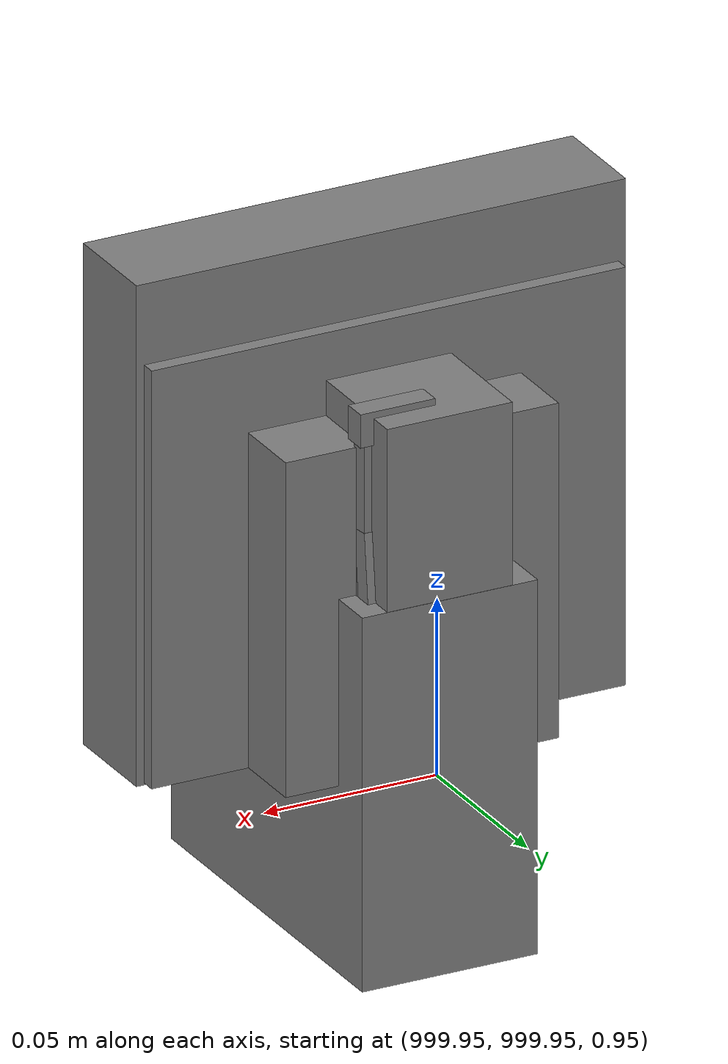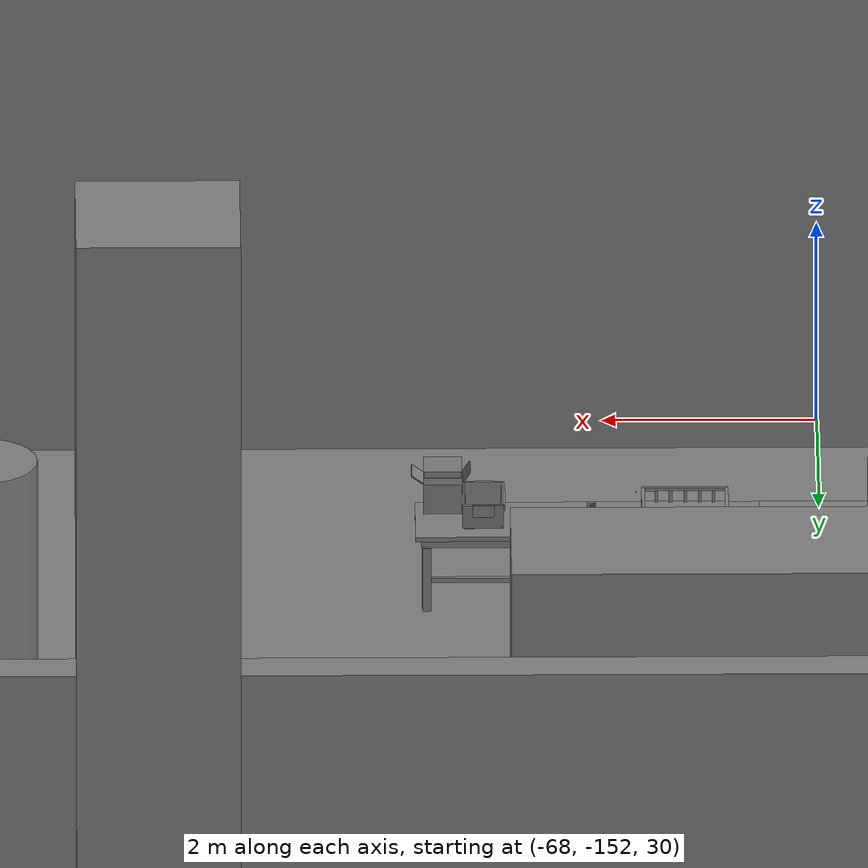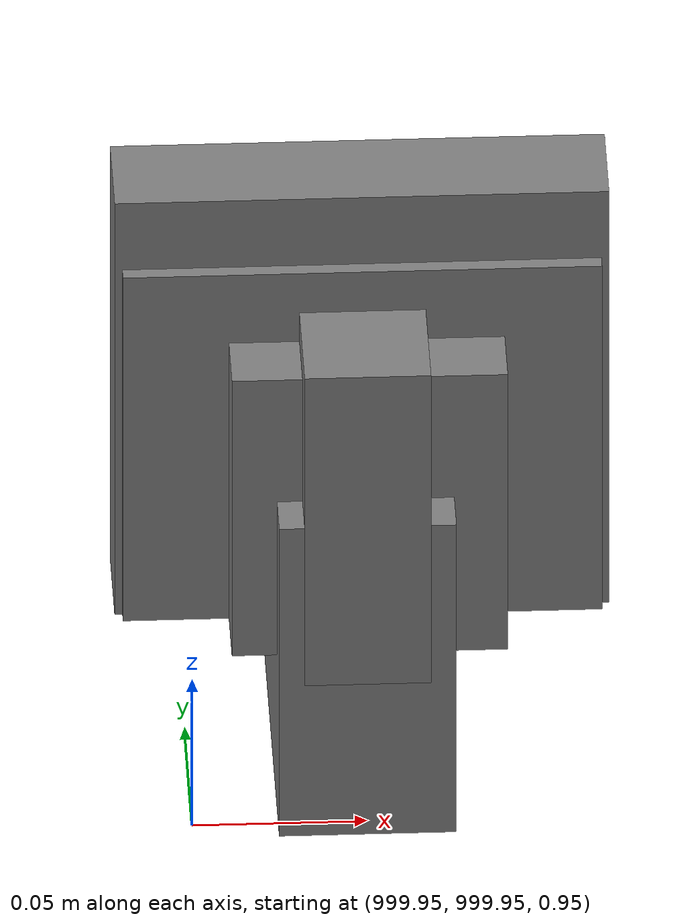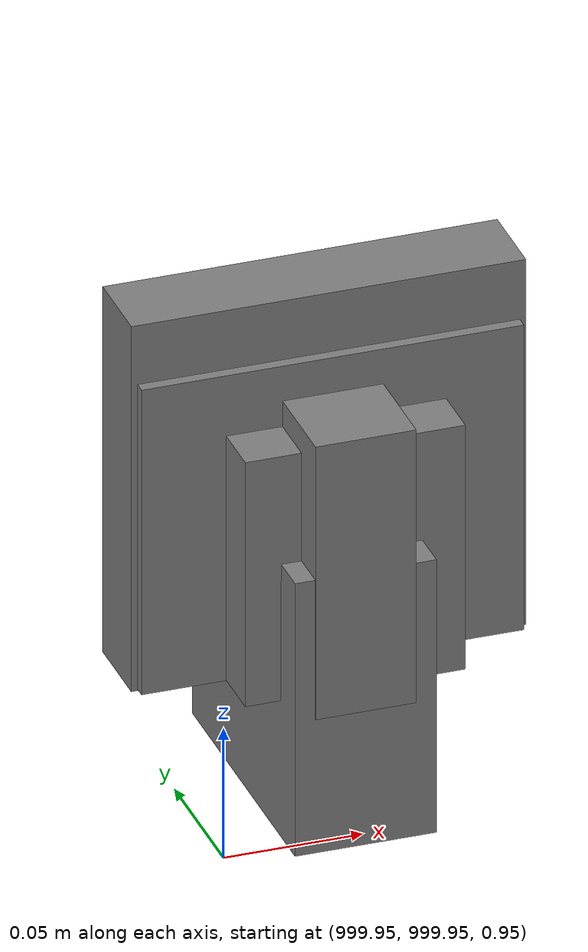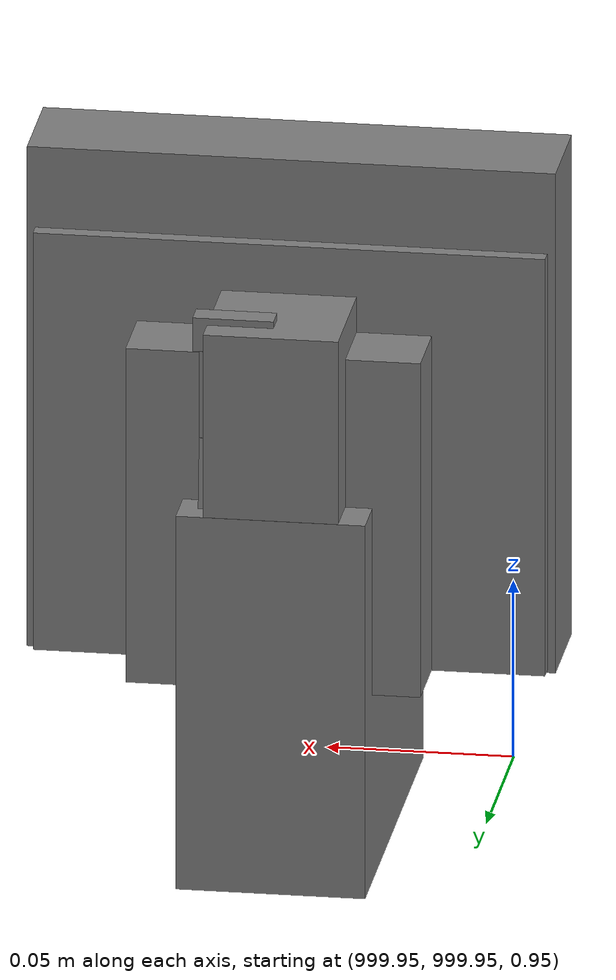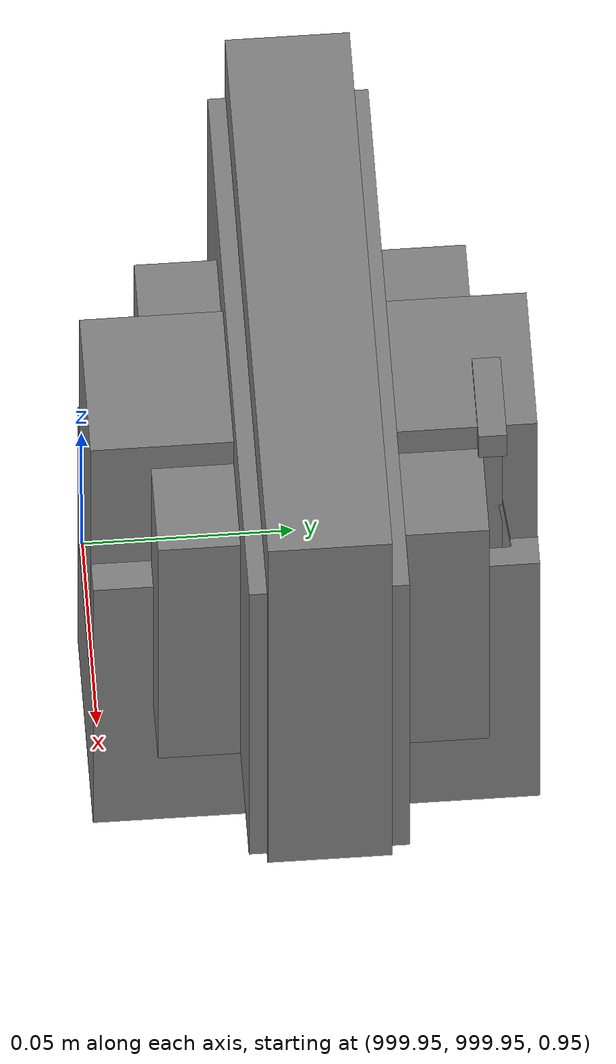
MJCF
<mujoco>
    <option gravity="0.000000000 0.000000000 -9.810000420" timestep="0.0049999999" integrator="implicitfast" density="1.225" viscosity="1.8000001e-05" noslip_iterations="10" iterations="100" sdf_iterations="50">
        <flag multiccd="disable"/>
    </option>
    <size memory="1000M"/>
    <compiler coordinate="local"/>
    <worldbody>
        <light cutoff="30" pos="0 1 1" dir="0 -1 -2"/>
        <light cutoff="30" pos="0 -1 1" dir="0 1 -2"/>
        <body pos="-64.866622925 -149.383972168 30.183746338" euler="89.999984741 89.999946594 0.000000000" name="openloong_gripper_2f85_fix_base_usda_bluebox_01">
            <geom contype="1" conaffinity="1" density="1000" type="box" material="" rgba="0.500000000 0.500000000 0.500000000 1.000000000" solimp="0.899999976 0.949999988 0.001000000" friction="1.000000000 0.005000000 0.000100000" solref="0.020000000 1.000000000" margin="0" condim="3" group="0" pos="0.276580811 0.187225342 0.000068665" quat="0.707106948 0.000077471 0.707106352 0.000077486" size="0.100000001 0.057999998 0.010000000" name="openloong_gripper_2f85_fix_base_usda_geom_F2EB9663_1DEF_4368_81C2_9C06069C4E5E"/>
            <geom contype="1" conaffinity="1" density="1000" type="box" material="" rgba="0.500000000 0.500000000 0.500000000 1.000000000" solimp="0.899999976 0.949999988 0.001000000" friction="1.000000000 0.005000000 0.000100000" solref="0.020000000 1.000000000" margin="0" condim="3" group="0" pos="0.000000000 0.002883911 0.000000000" quat="0.999999881 0.000000000 0.000000000 0.000000000" size="0.254000008 0.003000000 0.172000006" name="openloong_gripper_2f85_fix_base_usda_geom_B725EF83_33E4_4C68_8697_A40934F3A922"/>
            <geom contype="1" conaffinity="1" density="1000" type="box" material="" rgba="0.500000000 0.500000000 0.500000000 1.000000000" solimp="0.899999976 0.949999988 0.001000000" friction="1.000000000 0.005000000 0.000100000" solref="0.020000000 1.000000000" margin="0" condim="3" group="0" pos="0.000000000 0.124874115 0.173484802" quat="0.999796331 0.020176515 -0.000000015 0.000000030" size="0.259999990 0.119999997 0.007000000" name="openloong_gripper_2f85_fix_base_usda_geom_25A188D1_46C3_4B8A_BF1F_4738B1E77F28"/>
            <geom contype="1" conaffinity="1" density="1000" type="box" material="" rgba="0.500000000 0.500000000 0.500000000 1.000000000" solimp="0.899999976 0.949999988 0.001000000" friction="1.000000000 0.005000000 0.000100000" solref="0.020000000 1.000000000" margin="0" condim="3" group="0" pos="0.000000000 0.124874115 -0.173469543" quat="0.999796331 -0.020176545 -0.000000015 0.000000000" size="0.259999990 0.119999997 0.007000000" name="openloong_gripper_2f85_fix_base_usda_geom_7CC10316_AD31_4CA8_9DC8_1F6EC98638D7"/>
            <geom contype="1" conaffinity="1" density="1000" type="box" material="" rgba="0.500000000 0.500000000 0.500000000 1.000000000" solimp="0.899999976 0.949999988 0.001000000" friction="1.000000000 0.005000000 0.000100000" solref="0.020000000 1.000000000" margin="0" condim="3" group="0" pos="0.000000000 0.214008331 0.188980103" quat="0.999912977 0.013176724 0.000000015 0.000000000" size="0.259999990 0.029999999 0.012500000" name="openloong_gripper_2f85_fix_base_usda_geom_A0ADDB2A_5CAE_42AF_9163_7389D85C9F42"/>
            <geom contype="1" conaffinity="1" density="1000" type="box" material="" rgba="0.500000000 0.500000000 0.500000000 1.000000000" solimp="0.899999976 0.949999988 0.001000000" friction="1.000000000 0.005000000 0.000100000" solref="0.020000000 1.000000000" margin="0" condim="3" group="0" pos="-0.258361816 0.125289917 0.001876831" quat="0.702796936 -0.020792112 0.710783124 0.020769298" size="0.189999998 0.119999997 0.009000000" name="openloong_gripper_2f85_fix_base_usda_geom_39C7FBBE_B0BA_428F_99B4_0B6210950704"/>
            <geom contype="1" conaffinity="1" density="1000" type="box" material="" rgba="0.500000000 0.500000000 0.500000000 1.000000000" solimp="0.899999976 0.949999988 0.001000000" friction="1.000000000 0.005000000 0.000100000" solref="0.020000000 1.000000000" margin="0" condim="3" group="0" pos="0.000000000 0.214008331 -0.188980103" quat="0.999912977 -0.013176769 0.000000030 0.000000015" size="0.259999990 0.029999999 0.012500000" name="openloong_gripper_2f85_fix_base_usda_geom_216BCFFC_BE32_4E60_8BD0_EB7037E72EED"/>
            <geom contype="1" conaffinity="1" density="1000" type="box" material="" rgba="0.500000000 0.500000000 0.500000000 1.000000000" solimp="0.899999976 0.949999988 0.001000000" friction="1.000000000 0.005000000 0.000100000" solref="0.020000000 1.000000000" margin="0" condim="3" group="0" pos="-0.276611328 0.187225342 0.000068665" quat="0.707106650 0.000077441 0.707106709 0.000077456" size="0.100000001 0.057999998 0.010000000" name="openloong_gripper_2f85_fix_base_usda_geom_477D7F86_3E9C_4F9A_AA6F_35B1B922C177"/>
            <geom contype="1" conaffinity="1" density="1000" type="box" material="" rgba="0.500000000 0.500000000 0.500000000 1.000000000" solimp="0.899999976 0.949999988 0.001000000" friction="1.000000000 0.005000000 0.000100000" solref="0.020000000 1.000000000" margin="0" condim="3" group="0" pos="0.258331299 0.125289917 0.001876831" quat="0.702851415 0.018856421 0.710823774 -0.019329369" size="0.189999998 0.119999997 0.009000000" name="openloong_gripper_2f85_fix_base_usda_geom_2668842E_91EB_4835_A816_BC6A80BD5114"/>
            <freejoint name="openloong_gripper_2f85_fix_base_usda_bluebox_01_joint"/>
            <site size="0.005000000 0.005000000 0.005000000" rgba="0.500000000 0.500000000 0.500000000 1.000000000" pos="0.000000000 0.000000000 0.000000000" quat="0.999961913 0.008726534 0.000000000 0.000000000" group="0" type="sphere" name="openloong_gripper_2f85_fix_base_usda_bluebox_01site"/>
        </body>
        <body pos="-64.496299744 -149.491867065 30.235729218" euler="0.000000000 0.000000000 89.999946594" name="openloong_gripper_2f85_fix_base_usda_cardboardbox_01">
            <geom contype="1" conaffinity="1" density="1000" type="box" material="" rgba="0.500000000 0.500000000 0.500000000 1.000000000" solimp="0.899999976 0.949999988 0.001000000" friction="1.000000000 0.005000000 0.000100000" solref="0.020000000 1.000000000" margin="0" condim="3" group="0" pos="-0.003166199 -0.004086494 0.005052090" quat="1.000000000 0.000000000 0.000000000 0.000000000" size="0.142499998 0.177500010 0.005000000" name="openloong_gripper_2f85_fix_base_usda_geom_6640A3D3_9FEF_42B0_8A47_ACE9D16DB08B"/>
            <geom contype="1" conaffinity="1" density="1000" type="box" material="" rgba="0.500000000 0.500000000 0.500000000 1.000000000" solimp="0.899999976 0.949999988 0.001000000" friction="1.000000000 0.005000000 0.000100000" solref="0.020000000 1.000000000" margin="0" condim="3" group="0" pos="-0.003166199 0.170316696 0.150570869" quat="1.000000000 0.000000000 0.000000000 0.000000000" size="0.142499998 0.005000000 0.149999991" name="openloong_gripper_2f85_fix_base_usda_geom_4C74F2FF_D57A_47A5_A71D_90040215D9DA"/>
            <geom contype="1" conaffinity="1" density="1000" type="box" material="" rgba="0.500000000 0.500000000 0.500000000 1.000000000" solimp="0.899999976 0.949999988 0.001000000" friction="1.000000000 0.005000000 0.000100000" solref="0.020000000 1.000000000" margin="0" condim="3" group="0" pos="-0.147399902 -0.005307198 0.150570869" quat="1.000000000 0.000000000 0.000000000 0.000000000" size="0.005000000 0.177500010 0.149999991" name="openloong_gripper_2f85_fix_base_usda_geom_0677D172_C4A4_4EB2_8BBA_3964D42ABADD"/>
            <geom contype="1" conaffinity="1" density="1000" type="box" material="" rgba="0.500000000 0.500000000 0.500000000 1.000000000" solimp="0.899999976 0.949999988 0.001000000" friction="1.000000000 0.005000000 0.000100000" solref="0.020000000 1.000000000" margin="0" condim="3" group="0" pos="0.140275955 -0.005307198 0.150570869" quat="1.000000000 0.000000000 0.000000000 0.000000000" size="0.005000000 0.177500010 0.149999991" name="openloong_gripper_2f85_fix_base_usda_geom_DDC1F99D_8F32_4B90_8CD0_032B7C2BDF6E"/>
            <geom contype="1" conaffinity="1" density="1000" type="box" material="" rgba="0.500000000 0.500000000 0.500000000 1.000000000" solimp="0.899999976 0.949999988 0.001000000" friction="1.000000000 0.005000000 0.000100000" solref="0.020000000 1.000000000" margin="0" condim="3" group="0" pos="-0.003166199 -0.181550980 0.150570869" quat="1.000000000 0.000000000 0.000000000 0.000000000" size="0.142499998 0.005000000 0.149999991" name="openloong_gripper_2f85_fix_base_usda_geom_22DF20BC_E17A_4A10_A705_9A63E55AB232"/>
            <freejoint name="openloong_gripper_2f85_fix_base_usda_cardboardbox_01_joint"/>
            <site size="0.005000000 0.005000000 0.005000000" rgba="0.500000000 0.500000000 0.500000000 1.000000000" pos="0.000000000 0.000000000 0.000000000" quat="0.999961913 0.008726535 0.000000000 0.000000000" group="0" type="sphere" name="openloong_gripper_2f85_fix_base_usda_site_284456D3_F920_4B29_AA87_14A1C94E2AA1"/>
            <body pos="0.139160156 -0.004048347 0.301930904" euler="-179.999954224 49.383502960 179.999954224" name="openloong_gripper_2f85_fix_base_usda_A1_006">
                <geom contype="1" conaffinity="1" density="1000" type="box" material="" rgba="0.500000000 0.500000000 0.500000000 1.000000000" solimp="0.899999976 0.949999988 0.001000000" friction="1.000000000 0.005000000 0.000100000" solref="0.020000000 1.000000000" margin="0" condim="3" group="0" pos="-0.071587563 0.000009537 0.001745224" quat="0.999999881 0.000000000 0.000000000 0.000000000" size="0.071249999 0.179999992 0.002500000" name="openloong_gripper_2f85_fix_base_usda_geom_2589E571_F427_4CEB_BBBF_2A771EA9D722"/>
                <joint armature="0" stiffness="0.07" damping="0.0099999998" axis="0.000000 1.000000 0.000000" type="hinge" name="openloong_gripper_2f85_fix_base_usda_A1_006"/>
            </body>
            <body pos="-0.145902634 -0.004086494 0.301938057" euler="-180.000000000 -60.000011444 -180.000000000" name="openloong_gripper_2f85_fix_base_usda_A2_006">
                <geom contype="1" conaffinity="1" density="1000" type="box" material="" rgba="0.500000000 0.500000000 0.500000000 1.000000000" solimp="0.899999976 0.949999988 0.001000000" friction="1.000000000 0.005000000 0.000100000" solref="0.020000000 1.000000000" margin="0" condim="3" group="0" pos="0.071268082 0.000009537 0.002717972" quat="0.000002921 0.000000000 -0.000000030 0.999999881" size="0.071249999 0.179999992 0.002500000" name="openloong_gripper_2f85_fix_base_usda_geom_1B0AACFD_5384_4AEC_8F1E_44B8C0AED5F6"/>
                <joint armature="0" stiffness="0.07" damping="0.0099999998" axis="0.000000 1.000000 0.000000" type="hinge" name="openloong_gripper_2f85_fix_base_usda_A2_006"/>
            </body>
            <body pos="-0.003385544 0.175991058 0.301930904" euler="-125.858116150 -0.000004561 0.000002331" name="openloong_gripper_2f85_fix_base_usda_B2_006">
                <geom contype="1" conaffinity="1" density="1000" type="box" material="" rgba="0.500000000 0.500000000 0.500000000 1.000000000" solimp="0.899999976 0.949999988 0.001000000" friction="1.000000000 0.005000000 0.000100000" solref="0.020000000 1.000000000" margin="0" condim="3" group="0" pos="0.000009537 -0.070939064 -0.002470016" quat="0.999614120 0.027776197 -0.000000015 0.000000030" size="0.137500003 0.064999998 0.005000000" name="openloong_gripper_2f85_fix_base_usda_geom_624291AD_4EC4_4998_A0E4_C7BDBB6CCF9D"/>
                <joint armature="0" stiffness="0.07" damping="0.0099999998" axis="1.000000 0.000000 0.000000" type="hinge" name="openloong_gripper_2f85_fix_base_usda_B2_006"/>
            </body>
            <body pos="-0.003385544 -0.184140205 0.301938057" euler="147.805557251 0.000000000 0.000000000" name="openloong_gripper_2f85_fix_base_usda_B1_006">
                <geom contype="1" conaffinity="1" density="1000" type="box" material="" rgba="0.500000000 0.500000000 0.500000000 1.000000000" solimp="0.899999976 0.949999988 0.001000000" friction="1.000000000 0.005000000 0.000100000" solref="0.020000000 1.000000000" margin="0" condim="3" group="0" pos="-0.000028610 0.070202351 -0.002703667" quat="0.999614179 -0.027776167 0.000000000 0.000000000" size="0.137500003 0.064999998 0.005000000" name="openloong_gripper_2f85_fix_base_usda_geom_8BB7359B_E871_44CE_B482_7E4185B56BFC"/>
                <joint armature="0" stiffness="0.07" damping="0.0099999998" axis="1.000000 0.000000 0.000000" type="hinge" name="openloong_gripper_2f85_fix_base_usda_B1_006"/>
            </body>
        </body>
        <body pos="-65.882858276 -149.481979370 30.229999542" euler="-64.487716675 0.000000000 0.000000000" name="openloong_gripper_2f85_fix_base_usda_Barcode">
            <geom contype="1" conaffinity="1" density="1000" type="box" material="" rgba="0.500000000 0.500000000 0.500000000 1.000000000" solimp="0.899999976 0.949999988 0.001000000" friction="1.000000000 0.005000000 0.000100000" solref="0.020000000 1.000000000" margin="0" condim="3" group="0" pos="0.000000000 0.013038635 0.001419067" quat="0.000000000 0.000000000 0.000000000 1.000000119" size="0.034000002 0.010000000 0.017999999" name="openloong_gripper_2f85_fix_base_usda_geom_450208B5_601C_4094_AE6D_592B73E3AD5E"/>
            <geom contype="1" conaffinity="1" density="1000" type="box" material="" rgba="0.500000000 0.500000000 0.500000000 1.000000000" solimp="0.899999976 0.949999988 0.001000000" friction="1.000000000 0.005000000 0.000100000" solref="0.020000000 1.000000000" margin="0" condim="3" group="0" pos="0.000000000 -0.035301208 -0.007095337" quat="0.000000000 0.000000000 -0.043619365 0.999048233" size="0.028999999 0.010000000 0.020000000" name="openloong_gripper_2f85_fix_base_usda_geom_6E6D238B_118A_4B9A_9F4B_072476F5E8EF"/>
            <geom contype="1" conaffinity="1" density="1000" type="box" material="" rgba="0.500000000 0.500000000 0.500000000 1.000000000" solimp="0.899999976 0.949999988 0.001000000" friction="1.000000000 0.005000000 0.000100000" solref="0.020000000 1.000000000" margin="0" condim="3" group="0" pos="0.000000000 -0.043411255 -0.011749268" quat="0.922262907 0.386563420 0.000000000 0.000000000" size="0.026000001 0.010000000 0.020000000" name="openloong_gripper_2f85_fix_base_usda_geom_3A1DA76D_EEEE_4181_BF26_C9400C6750AE"/>
            <geom contype="1" conaffinity="1" density="1000" type="box" material="" rgba="0.500000000 0.500000000 0.500000000 1.000000000" solimp="0.899999976 0.949999988 0.001000000" friction="1.000000000 0.005000000 0.000100000" solref="0.020000000 1.000000000" margin="0" condim="3" group="0" pos="0.000000000 -0.016967773 -0.031860352" quat="0.000000000 0.000000000 0.000000000 1.000000119" size="0.008000000 0.010000000 0.013000000" name="openloong_gripper_2f85_fix_base_usda_geom_526CCC17_BD19_471A_9E59_D9365E019B04"/>
            <geom contype="1" conaffinity="1" density="1000" type="box" material="" rgba="0.500000000 0.500000000 0.500000000 1.000000000" solimp="0.899999976 0.949999988 0.001000000" friction="1.000000000 0.005000000 0.000100000" solref="0.020000000 1.000000000" margin="0" condim="3" group="0" pos="0.000000000 -0.001869202 0.000312805" quat="0.953716993 0.300705761 0.000000000 0.000000000" size="0.032000002 0.010000000 0.018999999" name="openloong_gripper_2f85_fix_base_usda_geom_829079A2_D815_4CCD_81B2_C51E87F7F921"/>
            <geom contype="1" conaffinity="1" density="1000" type="box" material="" rgba="0.500000000 0.500000000 0.500000000 1.000000000" solimp="0.899999976 0.949999988 0.001000000" friction="1.000000000 0.005000000 0.000100000" solref="0.020000000 1.000000000" margin="0" condim="3" group="0" pos="0.000000000 -0.019531250 -0.003173828" quat="0.953716993 0.300705761 0.000000000 0.000000000" size="0.030999999 0.010000000 0.020000000" name="openloong_gripper_2f85_fix_base_usda_geom_188046CC_BCF9_4357_A19D_576E60F30AFD"/>
            <geom contype="1" conaffinity="1" density="1000" type="box" material="" rgba="0.500000000 0.500000000 0.500000000 1.000000000" solimp="0.899999976 0.949999988 0.001000000" friction="1.000000000 0.005000000 0.000100000" solref="0.020000000 1.000000000" margin="0" condim="3" group="0" pos="0.000000000 -0.035301208 -0.007095337" quat="0.953716993 0.300705761 0.000000000 0.000000000" size="0.028999999 0.010000000 0.020000000" name="openloong_gripper_2f85_fix_base_usda_geom_FAEE9A25_CA7E_4E99_BC95_EB9D623A35F5"/>
            <geom contype="1" conaffinity="1" density="1000" type="box" material="" rgba="0.500000000 0.500000000 0.500000000 1.000000000" solimp="0.899999976 0.949999988 0.001000000" friction="1.000000000 0.005000000 0.000100000" solref="0.020000000 1.000000000" margin="0" condim="3" group="0" pos="0.000000000 -0.042617798 -0.071121216" quat="0.000000000 0.000000000 0.000000000 1.000000119" size="0.013000000 0.021000000 0.059999999" name="openloong_gripper_2f85_fix_base_usda_geom_D433EAB2_617F_4AFB_96F0_37F2851B14B0"/>
            <freejoint name="openloong_gripper_2f85_fix_base_usda_Barcode_joint"/>
            <site size="0.005000000 0.005000000 0.005000000" rgba="0.500000000 0.500000000 0.500000000 1.000000000" pos="0.000000000 0.000000000 0.000000000" quat="1.000000000 0.000000000 0.000000000 0.000000000" group="0" type="sphere" name="openloong_gripper_2f85_fix_base_usda_Barcode_site"/>
        </body>
        <body pos="-66.745018005 -149.392349243 30.184000015" euler="0.000000000 0.000000000 89.999946594" name="[22332024290161]_Basket_01">
            <geom contype="1" conaffinity="1" density="1000" type="box" material="" rgba="0.500000000 0.500000000 0.500000000 1.000000000" solimp="0.899999976 0.949999988 0.001000000" friction="1.000000000 0.005000000 0.000100000" solref="0.020000000 1.000000000" margin="0" condim="3" group="0" pos="-0.052425385 0.389207840 0.089787483" quat="0.707107008 0.000000000 0.000000000 0.707106411" size="0.014249999 0.014249999 0.059999999" name="[22332024290161]_geom_6DF73D5B_CE85_4C51_A376_1E5C31496B0E"/>
            <geom contype="1" conaffinity="1" density="1000" type="box" material="" rgba="0.500000000 0.500000000 0.500000000 1.000000000" solimp="0.899999976 0.949999988 0.001000000" friction="1.000000000 0.005000000 0.000100000" solref="0.020000000 1.000000000" margin="0" condim="3" group="0" pos="0.264015198 -0.133043289 0.089787483" quat="0.707107008 0.000000000 0.000000000 0.707106411" size="0.014249999 0.014249999 0.059999999" name="[22332024290161]_geom_655D9086_1D73_4416_9F27_4B469B3353A2"/>
            <geom contype="1" conaffinity="1" density="1000" type="box" material="" rgba="0.500000000 0.500000000 0.500000000 1.000000000" solimp="0.899999976 0.949999988 0.001000000" friction="1.000000000 0.005000000 0.000100000" solref="0.020000000 1.000000000" margin="0" condim="3" group="0" pos="-0.264015198 -0.265548706 0.089793205" quat="0.707107008 0.000000000 0.000000000 0.707106411" size="0.014249999 0.014249999 0.059999999" name="[22332024290161]_geom_7F410DA7_7D48_4CF9_A361_C3BA21AAA778"/>
            <geom contype="1" conaffinity="1" density="1000" type="box" material="" rgba="0.500000000 0.500000000 0.500000000 1.000000000" solimp="0.899999976 0.949999988 0.001000000" friction="1.000000000 0.005000000 0.000100000" solref="0.020000000 1.000000000" margin="0" condim="3" group="0" pos="-0.160263062 -0.389322281 0.089793205" quat="0.707107008 0.000000000 0.000000000 0.707106411" size="0.014249999 0.014249999 0.059999999" name="[22332024290161]_geom_C8F40BED_9B69_4175_BFC2_0D5A66F409DA"/>
            <geom contype="1" conaffinity="1" density="1000" type="box" material="" rgba="0.500000000 0.500000000 0.500000000 1.000000000" solimp="0.899999976 0.949999988 0.001000000" friction="1.000000000 0.005000000 0.000100000" solref="0.020000000 1.000000000" margin="0" condim="3" group="0" pos="0.162265778 -0.389322281 0.089787483" quat="0.707107008 0.000000000 0.000000000 0.707106411" size="0.014249999 0.014249999 0.059999999" name="[22332024290161]_geom_89CDDB4F_3BFF_4E74_AED6_B94B595EC22A"/>
            <geom contype="1" conaffinity="1" density="1000" type="box" material="" rgba="0.500000000 0.500000000 0.500000000 1.000000000" solimp="0.899999976 0.949999988 0.001000000" friction="1.000000000 0.005000000 0.000100000" solref="0.020000000 1.000000000" margin="0" condim="3" group="0" pos="0.264015198 0.389207840 0.089787483" quat="0.707107008 0.000000000 0.000000000 0.707106411" size="0.014249999 0.014249999 0.059999999" name="[22332024290161]_geom_F6D1ABBF_91F0_48BD_89E7_15FB24DAC9A2"/>
            <geom contype="1" conaffinity="1" density="1000" type="box" material="" rgba="0.500000000 0.500000000 0.500000000 1.000000000" solimp="0.899999976 0.949999988 0.001000000" friction="1.000000000 0.005000000 0.000100000" solref="0.020000000 1.000000000" margin="0" condim="3" group="0" pos="-0.264015198 -0.133043289 0.089793205" quat="0.707107008 0.000000000 0.000000000 0.707106411" size="0.014249999 0.014249999 0.059999999" name="[22332024290161]_geom_8877DCB2_05A1_48DB_BEB9_62F511EB67BC"/>
            <geom contype="1" conaffinity="1" density="1000" type="box" material="" rgba="0.500000000 0.500000000 0.500000000 1.000000000" solimp="0.899999976 0.949999988 0.001000000" friction="1.000000000 0.005000000 0.000100000" solref="0.020000000 1.000000000" margin="0" condim="3" group="0" pos="-0.264026642 0.269256592 0.089793205" quat="0.707107008 0.000000000 0.000000000 0.707106411" size="0.014249999 0.014249999 0.059999999" name="[22332024290161]_geom_302FAA4A_D115_420F_A862_B7A902698A15"/>
            <geom contype="1" conaffinity="1" density="1000" type="box" material="" rgba="0.500000000 0.500000000 0.500000000 1.000000000" solimp="0.899999976 0.949999988 0.001000000" friction="1.000000000 0.005000000 0.000100000" solref="0.020000000 1.000000000" margin="0" condim="3" group="0" pos="0.054462433 0.389207840 0.089787483" quat="0.707107008 0.000000000 0.000000000 0.707106411" size="0.014249999 0.014249999 0.059999999" name="[22332024290161]_geom_5B302D49_7D30_4EF1_BF39_843490D563DE"/>
            <geom contype="1" conaffinity="1" density="1000" type="box" material="" rgba="0.500000000 0.500000000 0.500000000 1.000000000" solimp="0.899999976 0.949999988 0.001000000" friction="1.000000000 0.005000000 0.000100000" solref="0.020000000 1.000000000" margin="0" condim="3" group="0" pos="0.054462433 -0.389322281 0.089787483" quat="0.707107008 0.000000000 0.000000000 0.707106411" size="0.014249999 0.014249999 0.059999999" name="[22332024290161]_geom_4024B29A_8271_4FC0_955E_03247DF29894"/>
            <geom contype="1" conaffinity="1" density="1000" type="box" material="" rgba="0.500000000 0.500000000 0.500000000 1.000000000" solimp="0.899999976 0.949999988 0.001000000" friction="1.000000000 0.005000000 0.000100000" solref="0.020000000 1.000000000" margin="0" condim="3" group="0" pos="0.264015198 0.269256592 0.089793205" quat="0.707107008 0.000000000 0.000000000 0.707106411" size="0.014249999 0.014249999 0.059999999" name="[22332024290161]_geom_3BEE25F4_5EF7_4FA9_A82E_79A19DDBCFC9"/>
            <geom contype="1" conaffinity="1" density="1000" type="box" material="" rgba="0.500000000 0.500000000 0.500000000 1.000000000" solimp="0.899999976 0.949999988 0.001000000" friction="1.000000000 0.005000000 0.000100000" solref="0.020000000 1.000000000" margin="0" condim="3" group="0" pos="0.264015198 -0.389322281 0.089787483" quat="0.707107008 0.000000000 0.000000000 0.707106411" size="0.014249999 0.014249999 0.059999999" name="[22332024290161]_geom_3C7041EB_2402_4BBC_A51E_D9540CB4EB43"/>
            <geom contype="1" conaffinity="1" density="1000" type="box" material="" rgba="0.500000000 0.500000000 0.500000000 1.000000000" solimp="0.899999976 0.949999988 0.001000000" friction="1.000000000 0.005000000 0.000100000" solref="0.020000000 1.000000000" margin="0" condim="3" group="0" pos="0.000000000 0.000000000 0.015998840" quat="0.707107008 0.000000000 0.000000000 0.707106411" size="0.403499991 0.279000014 0.015750000" name="[22332024290161]_geom_1A456E5A_B747_4765_B920_265F9456A321"/>
            <geom contype="1" conaffinity="1" density="1000" type="box" material="" rgba="0.500000000 0.500000000 0.500000000 1.000000000" solimp="0.899999976 0.949999988 0.001000000" friction="1.000000000 0.005000000 0.000100000" solref="0.020000000 1.000000000" margin="0" condim="3" group="0" pos="0.000000000 -0.389476776 0.163619041" quat="0.707107008 0.000000000 0.000000000 0.707106411" size="0.015000000 0.277500004 0.015750000" name="[22332024290161]_geom_25378D3E_1136_4D1F_A850_25ACE53CC5FC"/>
            <geom contype="1" conaffinity="1" density="1000" type="box" material="" rgba="0.500000000 0.500000000 0.500000000 1.000000000" solimp="0.899999976 0.949999988 0.001000000" friction="1.000000000 0.005000000 0.000100000" solref="0.020000000 1.000000000" margin="0" condim="3" group="0" pos="0.162265778 0.389207840 0.089787483" quat="0.707107008 0.000000000 0.000000000 0.707106411" size="0.014249999 0.014249999 0.059999999" name="[22332024290161]_geom_EBDAEA90_78B5_4374_BF62_B975C37E09B6"/>
            <geom contype="1" conaffinity="1" density="1000" type="box" material="" rgba="0.500000000 0.500000000 0.500000000 1.000000000" solimp="0.899999976 0.949999988 0.001000000" friction="1.000000000 0.005000000 0.000100000" solref="0.020000000 1.000000000" margin="0" condim="3" group="0" pos="0.000000000 0.389471054 0.163619041" quat="0.707107008 0.000000000 0.000000000 0.707106411" size="0.015000000 0.277500004 0.015750000" name="[22332024290161]_geom_6ED4E23E_0DC0_4E8A_8FF0_83E44EAD2B00"/>
            <geom contype="1" conaffinity="1" density="1000" type="box" material="" rgba="0.500000000 0.500000000 0.500000000 1.000000000" solimp="0.899999976 0.949999988 0.001000000" friction="1.000000000 0.005000000 0.000100000" solref="0.020000000 1.000000000" margin="0" condim="3" group="0" pos="-0.263511658 0.000000000 0.163619041" quat="0.707107008 0.000000000 0.000000000 0.707106411" size="0.403499991 0.015000000 0.015750000" name="[22332024290161]_geom_1AC82228_A10C_44B0_B5D3_F429F7E0E73A"/>
            <geom contype="1" conaffinity="1" density="1000" type="box" material="" rgba="0.500000000 0.500000000 0.500000000 1.000000000" solimp="0.899999976 0.949999988 0.001000000" friction="1.000000000 0.005000000 0.000100000" solref="0.020000000 1.000000000" margin="0" condim="3" group="0" pos="-0.264015198 0.141334534 0.089793205" quat="0.707107008 0.000000000 0.000000000 0.707106411" size="0.014249999 0.014249999 0.059999999" name="[22332024290161]_geom_9D9717E9_CB54_43F8_9B71_9B90E5A2BA6F"/>
            <geom contype="1" conaffinity="1" density="1000" type="box" material="" rgba="0.500000000 0.500000000 0.500000000 1.000000000" solimp="0.899999976 0.949999988 0.001000000" friction="1.000000000 0.005000000 0.000100000" solref="0.020000000 1.000000000" margin="0" condim="3" group="0" pos="0.264015198 -0.265548706 0.089787483" quat="0.707107008 0.000000000 0.000000000 0.707106411" size="0.014249999 0.014249999 0.059999999" name="[22332024290161]_geom_C8763116_4B74_40EF_9DF6_19A70A909B78"/>
            <geom contype="1" conaffinity="1" density="1000" type="box" material="" rgba="0.500000000 0.500000000 0.500000000 1.000000000" solimp="0.899999976 0.949999988 0.001000000" friction="1.000000000 0.005000000 0.000100000" solref="0.020000000 1.000000000" margin="0" condim="3" group="0" pos="-0.160263062 0.389207840 0.089787483" quat="0.707107008 0.000000000 0.000000000 0.707106411" size="0.014249999 0.014249999 0.059999999" name="[22332024290161]_geom_1404F225_1941_471C_8CF1_B9B87B6FD4F7"/>
            <geom contype="1" conaffinity="1" density="1000" type="box" material="" rgba="0.500000000 0.500000000 0.500000000 1.000000000" solimp="0.899999976 0.949999988 0.001000000" friction="1.000000000 0.005000000 0.000100000" solref="0.020000000 1.000000000" margin="0" condim="3" group="0" pos="-0.052425385 -0.389322281 0.089787483" quat="0.707107008 0.000000000 0.000000000 0.707106411" size="0.014249999 0.014249999 0.059999999" name="[22332024290161]_geom_735D81FE_02CB_4B13_BF37_3A6622284124"/>
            <geom contype="1" conaffinity="1" density="1000" type="box" material="" rgba="0.500000000 0.500000000 0.500000000 1.000000000" solimp="0.899999976 0.949999988 0.001000000" friction="1.000000000 0.005000000 0.000100000" solref="0.020000000 1.000000000" margin="0" condim="3" group="0" pos="-0.264026642 -0.389322281 0.089793205" quat="0.707107008 0.000000000 0.000000000 0.707106411" size="0.014249999 0.014249999 0.059999999" name="[22332024290161]_geom_64B501D5_D5E2_4B65_B80A_F00B283A8FFB"/>
            <geom contype="1" conaffinity="1" density="1000" type="box" material="" rgba="0.500000000 0.500000000 0.500000000 1.000000000" solimp="0.899999976 0.949999988 0.001000000" friction="1.000000000 0.005000000 0.000100000" solref="0.020000000 1.000000000" margin="0" condim="3" group="0" pos="0.264015198 0.141334534 0.089787483" quat="0.707107008 0.000000000 0.000000000 0.707106411" size="0.014249999 0.014249999 0.059999999" name="[22332024290161]_geom_4E4A3690_4B02_4DDA_8228_65616DD659F1"/>
            <geom contype="1" conaffinity="1" density="1000" type="box" material="" rgba="0.500000000 0.500000000 0.500000000 1.000000000" solimp="0.899999976 0.949999988 0.001000000" friction="1.000000000 0.005000000 0.000100000" solref="0.020000000 1.000000000" margin="0" condim="3" group="0" pos="-0.264015198 0.389207840 0.089793205" quat="0.707107008 0.000000000 0.000000000 0.707106411" size="0.014249999 0.014249999 0.059999999" name="[22332024290161]_geom_39D5B5C9_3ADB_41DD_8782_6D9BE0BD3EBA"/>
            <geom contype="1" conaffinity="1" density="1000" type="box" material="" rgba="0.500000000 0.500000000 0.500000000 1.000000000" solimp="0.899999976 0.949999988 0.001000000" friction="1.000000000 0.005000000 0.000100000" solref="0.020000000 1.000000000" margin="0" condim="3" group="0" pos="0.264015198 0.004480362 0.089787483" quat="0.707107008 0.000000000 0.000000000 0.707106411" size="0.014249999 0.014249999 0.059999999" name="[22332024290161]_geom_9167765A_1CDC_41C6_97B9_398A7951BD3E"/>
            <geom contype="1" conaffinity="1" density="1000" type="box" material="" rgba="0.500000000 0.500000000 0.500000000 1.000000000" solimp="0.899999976 0.949999988 0.001000000" friction="1.000000000 0.005000000 0.000100000" solref="0.020000000 1.000000000" margin="0" condim="3" group="0" pos="0.263694763 -0.000011444 0.163619041" quat="0.707107008 0.000000000 0.000000000 0.707106411" size="0.403499991 0.015000000 0.015750000" name="[22332024290161]_geom_D58C527A_1513_47DE_8B1D_F27BE7F0C5E8"/>
            <geom contype="1" conaffinity="1" density="1000" type="box" material="" rgba="0.500000000 0.500000000 0.500000000 1.000000000" solimp="0.899999976 0.949999988 0.001000000" friction="1.000000000 0.005000000 0.000100000" solref="0.020000000 1.000000000" margin="0" condim="3" group="0" pos="-0.264015198 0.004480362 0.089793205" quat="0.707107008 0.000000000 0.000000000 0.707106411" size="0.014249999 0.014249999 0.059999999" name="[22332024290161]_geom_C2A694AB_530D_46C2_9FEE_DF0152FAFABE"/>
            <freejoint name="[22332024290161]_joint_573BA157_FB76_4F52_9413_14EB7B801DE1"/>
        </body>
        <body pos="0.000000000 0.000000000 0.000000000" euler="0.000000000 0.000000000 0.000000000" name="Static Objects_Static Objects">
            <geom contype="1" conaffinity="1" density="1000" type="box" material="" rgba="0.500000000 0.500000000 0.500000000 1.000000000" solimp="0.899999976 0.949999988 0.001000000" friction="1.000000000 0.005000000 0.000100000" solref="0.020000000 1.000000000" margin="0" condim="3" group="0" pos="-67.544113159 -149.365814209 29.727830887" quat="0.500000417 0.499999970 0.499999553 0.499999970" size="0.381000012 0.319999993 0.041000001" name="Static Objects_geom_88872539_F98C_4689_8EBF_582E85B812CF"/>
            <geom contype="1" conaffinity="1" density="1000" type="box" material="" rgba="0.500000000 0.500000000 0.500000000 1.000000000" solimp="0.899999976 0.949999988 0.001000000" friction="1.000000000 0.005000000 0.000100000" solref="0.020000000 1.000000000" margin="0" condim="3" group="0" pos="-68.239501953 -149.365814209 30.086868286" quat="0.500000417 0.499999970 0.499999553 0.499999970" size="0.370999992 0.039500002 0.745000005" name="Static Objects_geom_19FC81D3_7621_41C5_957F_2F86039FCE24"/>
            <geom contype="1" conaffinity="1" density="1000" type="box" material="" rgba="0.500000000 0.500000000 0.500000000 1.000000000" solimp="0.899999976 0.949999988 0.001000000" friction="1.000000000 0.005000000 0.000100000" solref="0.020000000 1.000000000" margin="0" condim="3" group="0" pos="-68.239501953 -149.365814209 30.147235870" quat="0.500000417 0.499999970 0.499999553 0.499999970" size="0.400000006 0.022000000 0.800000012" name="Static Objects_geom_84614526_762B_4AF0_A736_D44AE49FD0CB"/>
            <geom contype="1" conaffinity="1" density="1000" type="box" material="" rgba="0.500000000 0.500000000 0.500000000 1.000000000" solimp="0.899999976 0.949999988 0.001000000" friction="1.000000000 0.005000000 0.000100000" solref="0.020000000 1.000000000" margin="0" condim="3" group="0" pos="-68.934890747 -149.365814209 29.727830887" quat="0.500000417 0.499999970 0.499999553 0.499999970" size="0.381000012 0.319999993 0.041000001" name="Static Objects_geom_BFB2583C_EC5F_4A17_BA46_408191C68595"/>
            <geom contype="1" conaffinity="1" density="1000" type="box" material="" rgba="0.500000000 0.500000000 0.500000000 1.000000000" solimp="0.899999976 0.949999988 0.001000000" friction="1.000000000 0.005000000 0.000100000" solref="0.020000000 1.000000000" margin="0" condim="3" group="0" pos="-68.239501953 -149.365814209 29.561563492" quat="0.500000417 0.499999970 0.499999553 0.499999970" size="0.020000000 0.022000000 0.660000026" name="Static Objects_geom_291F5E0B_96D4_4EF1_BDF2_70D760BEBB12"/>
            <geom contype="1" conaffinity="1" density="1000" type="box" material="" rgba="0.500000000 0.500000000 0.500000000 1.000000000" solimp="0.899999976 0.949999988 0.001000000" friction="1.000000000 0.005000000 0.000100000" solref="0.020000000 1.000000000" margin="0" condim="3" group="0" pos="-65.945671082 -149.365814209 29.727830887" quat="0.500000417 0.499999970 0.499999553 0.499999970" size="0.381000012 0.319999993 0.041000001" name="Static Objects_geom_2056DFFC_F077_4DAD_8823_1E19C5FC42CC"/>
            <geom contype="1" conaffinity="1" density="1000" type="box" material="" rgba="0.500000000 0.500000000 0.500000000 1.000000000" solimp="0.899999976 0.949999988 0.001000000" friction="1.000000000 0.005000000 0.000100000" solref="0.020000000 1.000000000" margin="0" condim="3" group="0" pos="-66.641059875 -149.365814209 30.086868286" quat="0.500000417 0.499999970 0.499999553 0.499999970" size="0.370999992 0.039500002 0.745000005" name="Static Objects_geom_DAF224FC_3D70_49B6_B11C_ACF894FB7460"/>
            <geom contype="1" conaffinity="1" density="1000" type="box" material="" rgba="0.500000000 0.500000000 0.500000000 1.000000000" solimp="0.899999976 0.949999988 0.001000000" friction="1.000000000 0.005000000 0.000100000" solref="0.020000000 1.000000000" margin="0" condim="3" group="0" pos="-66.641059875 -149.365814209 30.147235870" quat="0.500000417 0.499999970 0.499999553 0.499999970" size="0.400000006 0.022000000 0.800000012" name="Static Objects_geom_3DC20287_A99A_4C0A_A929_E21B2B0651CE"/>
            <geom contype="1" conaffinity="1" density="1000" type="box" material="" rgba="0.500000000 0.500000000 0.500000000 1.000000000" solimp="0.899999976 0.949999988 0.001000000" friction="1.000000000 0.005000000 0.000100000" solref="0.020000000 1.000000000" margin="0" condim="3" group="0" pos="-67.336448669 -149.365814209 29.727830887" quat="0.500000417 0.499999970 0.499999553 0.499999970" size="0.381000012 0.319999993 0.041000001" name="Static Objects_geom_D8543958_2F81_4098_831F_0306CDF9D761"/>
            <geom contype="1" conaffinity="1" density="1000" type="box" material="" rgba="0.500000000 0.500000000 0.500000000 1.000000000" solimp="0.899999976 0.949999988 0.001000000" friction="1.000000000 0.005000000 0.000100000" solref="0.020000000 1.000000000" margin="0" condim="3" group="0" pos="-66.641059875 -149.365814209 29.561563492" quat="0.500000417 0.499999970 0.499999553 0.499999970" size="0.020000000 0.022000000 0.660000026" name="Static Objects_geom_95FB9C77_DA15_4C9E_AAA5_5373D8AF951B"/>
            <geom contype="1" conaffinity="1" density="1000" type="box" material="" rgba="0.500000000 0.500000000 0.500000000 1.000000000" solimp="0.899999976 0.949999988 0.001000000" friction="1.000000000 0.005000000 0.000100000" solref="0.020000000 1.000000000" margin="0" condim="3" group="0" pos="-64.338577271 -149.365814209 29.727830887" quat="0.500000417 0.499999970 0.499999553 0.499999970" size="0.381000012 0.319999993 0.041000001" name="Static Objects_geom_BC527332_04FA_41E8_85CD_89A1D68ADCCD"/>
            <geom contype="1" conaffinity="1" density="1000" type="box" material="" rgba="0.500000000 0.500000000 0.500000000 1.000000000" solimp="0.899999976 0.949999988 0.001000000" friction="1.000000000 0.005000000 0.000100000" solref="0.020000000 1.000000000" margin="0" condim="3" group="0" pos="-65.033966064 -149.365814209 30.086868286" quat="0.500000417 0.499999970 0.499999553 0.499999970" size="0.370999992 0.039500002 0.745000005" name="Static Objects_geom_AA8469CD_676A_4786_AB06_F9433D8DB706"/>
            <geom contype="1" conaffinity="1" density="1000" type="box" material="" rgba="0.500000000 0.500000000 0.500000000 1.000000000" solimp="0.899999976 0.949999988 0.001000000" friction="1.000000000 0.005000000 0.000100000" solref="0.020000000 1.000000000" margin="0" condim="3" group="0" pos="-65.033966064 -149.365814209 30.147235870" quat="0.500000417 0.499999970 0.499999553 0.499999970" size="0.400000006 0.022000000 0.800000012" name="Static Objects_geom_D98138BD_53A2_4379_AA9B_6044E37DBF75"/>
            <geom contype="1" conaffinity="1" density="1000" type="box" material="" rgba="0.500000000 0.500000000 0.500000000 1.000000000" solimp="0.899999976 0.949999988 0.001000000" friction="1.000000000 0.005000000 0.000100000" solref="0.020000000 1.000000000" margin="0" condim="3" group="0" pos="-65.729354858 -149.365814209 29.727830887" quat="0.500000417 0.499999970 0.499999553 0.499999970" size="0.381000012 0.319999993 0.041000001" name="Static Objects_geom_FF546FAE_0C33_4FCF_AEB6_08F122ACB372"/>
            <geom contype="1" conaffinity="1" density="1000" type="box" material="" rgba="0.500000000 0.500000000 0.500000000 1.000000000" solimp="0.899999976 0.949999988 0.001000000" friction="1.000000000 0.005000000 0.000100000" solref="0.020000000 1.000000000" margin="0" condim="3" group="0" pos="-65.033966064 -149.365814209 29.561563492" quat="0.500000417 0.499999970 0.499999553 0.499999970" size="0.020000000 0.022000000 0.660000026" name="Static Objects_geom_F9B2E1A6_847E_4A9D_B3A2_90F5A80279DF"/>
            <geom contype="1" conaffinity="1" density="1000" type="box" material="" rgba="0.500000000 0.500000000 0.500000000 1.000000000" solimp="0.899999976 0.949999988 0.001000000" friction="1.000000000 0.005000000 0.000100000" solref="0.020000000 1.000000000" margin="0" condim="3" group="0" pos="-61.754566193 -137.853729248 33.906845093" quat="0.707107067 0.000000000 0.000000000 0.707106471" size="0.759999990 0.759999990 4.500000000" name="Static Objects_geom_E5547543_539D_44AD_A62B_56D0BFD3673F"/>
            <geom contype="1" conaffinity="1" density="1000" type="box" material="" rgba="0.500000000 0.500000000 0.500000000 1.000000000" solimp="0.899999976 0.949999988 0.001000000" friction="1.000000000 0.005000000 0.000100000" solref="0.020000000 1.000000000" margin="0" condim="3" group="0" pos="-57.511135101 -144.927108765 31.707921982" quat="1.000000000 0.000000000 0.000000000 0.000000000" size="0.200000003 8.000000000 2.299999952" name="Static Objects_geom_2D3EF52D_1C51_46F8_8B90_D63665DEF6E0"/>
            <geom contype="1" conaffinity="1" density="1000" type="box" material="" rgba="0.500000000 0.500000000 0.500000000 1.000000000" solimp="0.899999976 0.949999988 0.001000000" friction="1.000000000 0.005000000 0.000100000" solref="0.020000000 1.000000000" margin="0" condim="3" group="0" pos="-80.517646790 -157.574050903 31.688196182" quat="0.707107067 0.000000000 0.000000000 0.707106471" size="0.600000024 0.600000024 2.299999952" name="Static Objects_geom_F715FEB9_7F70_4A0C_9423_E7ACEF60D96E"/>
            <geom contype="1" conaffinity="1" density="1000" type="box" material="" rgba="0.500000000 0.500000000 0.500000000 1.000000000" solimp="0.899999976 0.949999988 0.001000000" friction="1.000000000 0.005000000 0.000100000" solref="0.020000000 1.000000000" margin="0" condim="3" group="0" pos="-80.711044312 -147.414932251 31.666158676" quat="1.000000000 0.000000000 0.000000000 0.000000000" size="0.200000003 10.000000000 2.299999952" name="Static Objects_geom_22FCF97A_F91B_44BB_9D54_1B0087F3CE42"/>
            <geom contype="1" conaffinity="1" density="1000" type="box" material="" rgba="0.500000000 0.500000000 0.500000000 1.000000000" solimp="0.899999976 0.949999988 0.001000000" friction="1.000000000 0.005000000 0.000100000" solref="0.020000000 1.000000000" margin="0" condim="3" group="0" pos="-57.687217712 -137.434692383 31.688196182" quat="0.707107067 0.000000000 0.000000000 0.707106471" size="0.600000024 0.600000024 2.299999952" name="Static Objects_geom_1FEDB72A_FB40_4D9C_9684_95DB0C68CD78"/>
            <geom contype="1" conaffinity="1" density="1000" type="box" material="" rgba="0.500000000 0.500000000 0.500000000 1.000000000" solimp="0.899999976 0.949999988 0.001000000" friction="1.000000000 0.005000000 0.000100000" solref="0.020000000 1.000000000" margin="0" condim="3" group="0" pos="-69.537033081 -140.263229370 31.714921951" quat="0.707107067 0.000000000 0.000000000 0.707106471" size="0.759999990 4.500000000 2.299999952" name="Static Objects_geom_3AE33674_26AB_44D4_B5E3_CF85E2021983"/>
            <geom contype="1" conaffinity="1" density="1000" type="box" material="" rgba="0.500000000 0.500000000 0.500000000 1.000000000" solimp="0.899999976 0.949999988 0.001000000" friction="1.000000000 0.005000000 0.000100000" solref="0.020000000 1.000000000" margin="0" condim="3" group="0" pos="-80.073638916 -137.853713989 33.906845093" quat="0.707107067 0.000000000 0.000000000 0.707106471" size="0.759999990 0.759999990 4.500000000" name="Static Objects_geom_8996774F_1096_4009_8DB4_CB0AE2359B7E"/>
            <geom contype="1" conaffinity="1" density="1000" type="box" material="" rgba="0.500000000 0.500000000 0.500000000 1.000000000" solimp="0.899999976 0.949999988 0.001000000" friction="1.000000000 0.005000000 0.000100000" solref="0.020000000 1.000000000" margin="0" condim="3" group="0" pos="-73.406707764 -155.734664917 31.707921982" quat="1.000000000 0.000000000 0.000000000 0.000000000" size="0.200000003 3.000000000 2.299999952" name="Static Objects_geom_F57C68EA_82D1_48BC_8864_6647A5AFDC2C"/>
            <geom contype="1" conaffinity="1" density="1000" type="box" material="" rgba="0.500000000 0.500000000 0.500000000 1.000000000" solimp="0.899999976 0.949999988 0.001000000" friction="1.000000000 0.005000000 0.000100000" solref="0.020000000 1.000000000" margin="0" condim="3" group="0" pos="-68.497543335 -137.448257446 31.707921982" quat="0.707107067 0.000000000 0.000000000 0.707106471" size="0.200000003 14.000000000 2.299999952" name="Static Objects_geom_61EA04BF_E1F5_4B7B_8B66_656B72612841"/>
            <geom contype="1" conaffinity="1" density="1000" type="cylinder" material="" rgba="0.500000000 0.500000000 0.500000000 1.000000000" solimp="0.899999976 0.949999988 0.001000000" friction="1.000000000 0.005000000 0.000100000" solref="0.020000000 1.000000000" margin="0" condim="3" group="0" pos="-68.868522644 -142.134506226 31.711090088" quat="0.707107067 0.000000000 0.000000000 0.707106471" size="0.509999990 2.299999952 1.000000000" name="Static Objects_geom_35B1B728_3965_4C90_A7F6_DE923B8CD5DD"/>
            <geom contype="1" conaffinity="1" density="1000" type="plane" material="" rgba="0.500000000 0.500000000 0.500000000 1.000000000" solimp="0.899999976 0.949999988 0.001000000" friction="1.000000000 0.005000000 0.000100000" solref="0.020000000 1.000000000" margin="0" condim="3" group="0" pos="-72.873703003 -147.131927490 29.409669876" quat="1.000000000 0.000000000 0.000000000 0.000000000" size="18.000000000 14.000000000 1.000000000" name="Static Objects_geom_C2DB6EE0_EF08_4D19_AD0A_953BEE1029A2"/>
            <geom contype="1" conaffinity="1" density="1000" type="box" material="" rgba="0.500000000 0.500000000 0.500000000 1.000000000" solimp="0.899999976 0.949999988 0.001000000" friction="1.000000000 0.005000000 0.000100000" solref="0.020000000 1.000000000" margin="0" condim="3" group="0" pos="-79.943580627 -157.782272339 31.707921982" quat="0.707107067 0.000000000 0.000000000 0.707106471" size="0.200000003 7.000000000 2.299999952" name="Static Objects_geom_1195D958_F6BC_4932_BBDC_288AE1E38794"/>
            <geom contype="1" conaffinity="1" density="1000" type="box" material="" rgba="0.500000000 0.500000000 0.500000000 1.000000000" solimp="0.899999976 0.949999988 0.001000000" friction="1.000000000 0.005000000 0.000100000" solref="0.020000000 1.000000000" margin="0" condim="3" group="0" pos="-65.421028137 -152.903442383 31.707921982" quat="0.707107067 0.000000000 0.000000000 0.707106471" size="0.200000003 7.800000191 2.299999952" name="Static Objects_geom_0008BB89_9018_4205_A9E1_DC30339E53D2"/>
            <geom contype="1" conaffinity="1" density="1000" type="box" material="" rgba="0.500000000 0.500000000 0.500000000 1.000000000" solimp="0.899999976 0.949999988 0.001000000" friction="1.000000000 0.005000000 0.000100000" solref="0.020000000 1.000000000" margin="0" condim="3" group="0" pos="-74.776908875 -149.964416504 31.688196182" quat="1.000000000 0.000000000 0.000000000 0.000000000" size="0.600000024 0.409999996 2.299999952" name="Static Objects_geom_B3D40A79_9358_415A_A353_D74581675BB9"/>
            <geom contype="1" conaffinity="1" density="1000" type="cylinder" material="" rgba="0.500000000 0.500000000 0.500000000 1.000000000" solimp="0.899999976 0.949999988 0.001000000" friction="1.000000000 0.005000000 0.000100000" solref="0.020000000 1.000000000" margin="0" condim="3" group="0" pos="-60.161884308 -142.134506226 31.711090088" quat="0.707107067 0.000000000 0.000000000 0.707106471" size="0.509999990 2.299999952 1.000000000" name="Static Objects_geom_3443B9AD_B627_4EB9_A083_E82A926C1A2A"/>
            <geom contype="1" conaffinity="1" density="1000" type="cylinder" material="" rgba="0.500000000 0.500000000 0.500000000 1.000000000" solimp="0.899999976 0.949999988 0.001000000" friction="1.000000000 0.005000000 0.000100000" solref="0.020000000 1.000000000" margin="0" condim="3" group="0" pos="-75.382453918 -149.963455200 31.711090088" quat="0.707107067 0.000000000 0.000000000 0.707106471" size="0.409999996 2.299999952 1.000000000" name="Static Objects_geom_6E5746D4_913D_46EC_AE03_03A6CFE0C64F"/>
            <geom contype="1" conaffinity="1" density="1000" type="cylinder" material="" rgba="0.500000000 0.500000000 0.500000000 1.000000000" solimp="0.899999976 0.949999988 0.001000000" friction="1.000000000 0.005000000 0.000100000" solref="0.020000000 1.000000000" margin="0" condim="3" group="0" pos="-74.154960632 -149.963455200 31.711090088" quat="0.707107067 0.000000000 0.000000000 0.707106471" size="0.409999996 2.299999952 1.000000000" name="Static Objects_geom_166C78C4_B144_47CB_85AF_844026836594"/>
            <geom contype="1" conaffinity="1" density="1000" type="cylinder" material="" rgba="0.500000000 0.500000000 0.500000000 1.000000000" solimp="0.899999976 0.949999988 0.001000000" friction="1.000000000 0.005000000 0.000100000" solref="0.020000000 1.000000000" margin="0" condim="3" group="0" pos="-77.566612244 -142.134506226 31.711090088" quat="0.707107067 0.000000000 0.000000000 0.707106471" size="0.509999990 2.299999952 1.000000000" name="Static Objects_geom_9DD7DD68_4AE9_48CA_9BD6_5DBEB79C8F2D"/>
        </body>
        <body pos="1000.000000000 1000.000000000 1.000000000" euler="0.000000000 0.000000000 180.000000000" name="openloong_gripper_2f85_fix_base_usda_wifi_box">
            <geom contype="1" conaffinity="1" density="1000" type="box" material="" rgba="0.500000000 0.500000000 0.500000000 1.000000000" solimp="0.899999976 0.949999988 0.001000000" friction="1.000000000 0.005000000 0.000100000" solref="0.020000000 1.000000000" margin="0" condim="3" group="0" pos="0.000000000 0.000000000 0.058978677" quat="0.000000000 0.000000047 0.000000000 1.000000000" size="0.068499997 0.018999999 0.059000000" name="openloong_gripper_2f85_fix_base_usda_geom_3B321086_2A21_4E75_9E01_1E59E0327289"/>
            <freejoint name="openloong_gripper_2f85_fix_base_usda_wifi_box_joint"/>
            <site size="0.005000000 0.005000000 0.005000000" rgba="0.500000000 0.500000000 0.500000000 1.000000000" pos="0.000000000 0.000000000 0.000000000" quat="0.999961913 0.008726500 0.000000000 0.000000000" group="0" type="sphere" name="openloong_gripper_2f85_fix_base_usda_wifi_boxsite"/>
        </body>
        <body pos="1000.000000000 999.999938965 1.000000000" euler="0.000000000 0.000000000 180.000000000" name="openloong_gripper_2f85_fix_base_usda_intelcore_i5">
            <geom contype="1" conaffinity="1" density="1000" type="box" material="" rgba="0.500000000 0.500000000 0.500000000 1.000000000" solimp="0.899999976 0.949999988 0.001000000" friction="1.000000000 0.005000000 0.000100000" solref="0.020000000 1.000000000" margin="0" condim="3" group="0" pos="0.000000000 0.000000000 0.051722717" quat="0.707106709 0.000000000 0.000000000 -0.707106769" size="0.052800000 0.018080002 0.052800000" name="openloong_gripper_2f85_fix_base_usda_geom_1B95A78E_44E1_48FF_BAE6_088FB5CBA89C"/>
            <freejoint name="openloong_gripper_2f85_fix_base_usda_intelcore_i5_joint"/>
            <site size="0.005000000 0.005000000 0.005000000" rgba="0.500000000 0.500000000 0.500000000 1.000000000" pos="0.000000000 0.000000000 0.000000000" quat="0.999961913 0.008726534 0.000000000 0.000000000" group="0" type="sphere" name="openloong_gripper_2f85_fix_base_usda_intelcore_i5site"/>
        </body>
        <body pos="-66.383308411 -149.578857422 31.163135529" euler="-20.513826370 -30.463167191 115.705375671" mocap="true" name="spotlight5_SpotLight"/>
        <body pos="-65.949783325 -149.374023438 31.170499802" euler="-101.344772339 -13.678638458 140.398117065" mocap="true" name="spotlight2_SpotLight"/>
        <body pos="1000.000000000 1000.000000000 1.000000000" euler="0.000011953 0.000005123 -179.999984741" name="openloong_gripper_2f85_fix_base_usda_intel_box">
            <geom contype="1" conaffinity="1" density="1000" type="box" material="" rgba="0.500000000 0.500000000 0.500000000 1.000000000" solimp="0.899999976 0.949999988 0.001000000" friction="1.000000000 0.005000000 0.000100000" solref="0.020000000 1.000000000" margin="0" condim="3" group="0" pos="0.000000000 -0.000067139 0.000082284" quat="0.707106709 0.000000225 0.000000253 0.707106650" size="0.052800003 0.025300000 0.052800003" name="openloong_gripper_2f85_fix_base_usda_geom_1F09B15D_0375_4C8C_9B8D_7A59E513ED0D"/>
            <freejoint name="openloong_gripper_2f85_fix_base_usda_intel_box_joint"/>
            <site size="0.005000000 0.005000000 0.005000000" rgba="0.500000000 0.500000000 0.500000000 1.000000000" pos="0.000000000 0.000000000 0.000000000" quat="0.999961913 0.008726500 0.000000000 0.000000000" group="0" type="sphere" name="openloong_gripper_2f85_fix_base_usda_intel_boxsite"/>
        </body>
        <body pos="1000.000000000 1000.000000000 1.000000000" euler="0.000000000 0.000000000 180.000000000" name="openloong_gripper_2f85_fix_base_usda_cpu_fan">
            <geom contype="1" conaffinity="1" density="1000" type="box" material="" rgba="0.500000000 0.500000000 0.500000000 1.000000000" solimp="0.899999976 0.949999988 0.001000000" friction="1.000000000 0.005000000 0.000100000" solref="0.020000000 1.000000000" margin="0" condim="3" group="0" pos="0.000000000 0.000000000 0.070034981" quat="0.000000000 0.000000000 0.000000000 1.000000000" size="0.070700005 0.014699999 0.070700005" name="openloong_gripper_2f85_fix_base_usda_geom_323B4120_C7A5_45EF_A52B_75FD302204FE"/>
            <freejoint name="openloong_gripper_2f85_fix_base_usda_cpu_fan_joint"/>
            <site size="0.005000000 0.005000000 0.005000000" rgba="0.500000000 0.500000000 0.500000000 1.000000000" pos="0.000000000 0.000000000 0.000000000" quat="0.999961913 0.008726535 0.000000000 0.000000000" group="0" type="sphere" name="openloong_gripper_2f85_fix_base_usda_cpu_fancsite"/>
        </body>
        <body pos="1000.000000000 1000.000000000 1.000000000" euler="0.000000000 0.000000000 180.000000000" name="openloong_gripper_2f85_fix_base_usda_battery_01">
            <geom contype="1" conaffinity="1" density="1000" type="box" material="" rgba="0.500000000 0.500000000 0.500000000 1.000000000" solimp="0.899999976 0.949999988 0.001000000" friction="1.000000000 0.005000000 0.000100000" solref="0.020000000 1.000000000" margin="0" condim="3" group="0" pos="-0.011123657 -0.041940309 0.101691343" quat="1.000000000 0.000000000 0.000000000 0.000000000" size="0.010800000 0.003375000 0.004725000" name="openloong_gripper_2f85_fix_base_usda_geom_81AEF039_8BAA_4ECB_96CF_DC33DEDC1E2B"/>
            <geom contype="1" conaffinity="1" density="1000" type="box" material="" rgba="0.500000000 0.500000000 0.500000000 1.000000000" solimp="0.899999976 0.949999988 0.001000000" friction="1.000000000 0.005000000 0.000100000" solref="0.020000000 1.000000000" margin="0" condim="3" group="0" pos="-0.010876465 -0.044247437 0.047066893" quat="0.998702705 -0.050920475 0.000000000 0.000000000" size="0.009450001 0.002700000 0.024975000" name="openloong_gripper_2f85_fix_base_usda_geom_B80F9B73_09F0_4330_86A1_B2312B720C3A"/>
            <geom contype="1" conaffinity="1" density="1000" type="box" material="" rgba="0.500000000 0.500000000 0.500000000 1.000000000" solimp="0.899999976 0.949999988 0.001000000" friction="1.000000000 0.005000000 0.000100000" solref="0.020000000 1.000000000" margin="0" condim="3" group="0" pos="-0.001235962 -0.000659180 0.047381196" quat="1.000000000 0.000000000 0.000000000 0.000000000" size="0.039420001 0.039150000 0.047250003" name="openloong_gripper_2f85_fix_base_usda_geom_7DCD0E0D_B9D8_4276_9BEC_5F601DB4B2FD"/>
            <geom contype="1" conaffinity="1" density="1000" type="box" material="" rgba="0.500000000 0.500000000 0.500000000 1.000000000" solimp="0.899999976 0.949999988 0.001000000" friction="1.000000000 0.005000000 0.000100000" solref="0.020000000 1.000000000" margin="0" condim="3" group="0" pos="-0.010876465 -0.039138794 0.009851727" quat="1.000000000 0.000000000 0.000000000 0.000000000" size="0.009450001 0.010800000 0.013500000" name="openloong_gripper_2f85_fix_base_usda_geom_B3721C03_65FB_4CCC_BF6F_2E77558829D8"/>
            <geom contype="1" conaffinity="1" density="1000" type="box" material="" rgba="0.500000000 0.500000000 0.500000000 1.000000000" solimp="0.899999976 0.949999988 0.001000000" friction="1.000000000 0.005000000 0.000100000" solref="0.020000000 1.000000000" margin="0" condim="3" group="0" pos="-0.010876465 -0.041528322 0.071508206" quat="1.000000000 0.000000000 0.000000000 0.000000000" size="0.009450001 0.002700000 0.027000001" name="openloong_gripper_2f85_fix_base_usda_geom_37E0E851_EF02_4A26_92DB_35A6ED23ED16"/>
            <freejoint name="openloong_gripper_2f85_fix_base_usda_battery_01_joint"/>
            <site size="0.005000000 0.005000000 0.005000000" rgba="0.500000000 0.500000000 0.500000000 1.000000000" pos="0.000000000 0.000000000 0.000000000" quat="0.999961913 0.008726500 0.000000000 0.000000000" group="0" type="sphere" name="openloong_gripper_2f85_fix_base_usda_battery_01site"/>
        </body>
        <body pos="-66.124061584 -149.724594116 31.169729233" euler="-11.655657768 45.567115784 109.284751892" mocap="true" name="spotlight4_SpotLight"/>
        <body pos="-66.291030884 -149.869689941 29.018842697" euler="0.000000000 0.000000000 89.999946594" mocap="true" name="openloong_gripper_2f85_fix_base_usda_leftHandMocap"/>
        <body pos="-66.291030884 -149.869689941 29.018842697" euler="0.000000000 0.000000000 89.999946594" mocap="true" name="openloong_gripper_2f85_fix_base_usda_rightHandMocap"/>
        <body pos="-66.291030884 -149.869689941 30.218843460" euler="0.000000000 0.000000000 89.999946594" name="openloong_gripper_2f85_fix_base_usda_base_link">
            <geom contype="1" conaffinity="1" density="1000" type="mesh" material="" rgba="0.783999979 0.783999979 0.783999979 1.000000000" solimp="0.899999976 0.949999988 0.001000000" friction="1.000000000 0.005000000 0.000100000" solref="0.020000000 1.000000000" margin="0" condim="3" group="3" mesh="base_link" pos="0.000000000 0.000000000 0.000000000" quat="1.000000000 0.000000000 0.000000000 0.000000000" size="1.000000000 1.000000000 1.000000000" name="openloong_gripper_2f85_fix_base_usda__geom_7_08E5B04E_7779_4D72_92BF_3B9F045CF6A5"/>
            <site size="0.005000000 0.005000000 0.005000000" rgba="0.500000000 0.500000000 0.500000000 1.000000000" pos="0.000000000 0.000000000 0.000000000" quat="1.000000000 0.000000000 0.000000000 0.000000000" group="0" type="sphere" name="openloong_gripper_2f85_fix_base_usda_imu"/>
            <inertial mass="22.447001" pos="-0.005664100 -0.001336700 0.238289997" diaginertia="0.374352545 0.277180195 0.220617250" quat="0.999247074 0.035235517 -0.015086859 0.006023135"/>
            <body pos="0.000000000 0.000000000 0.299997330" euler="0.000000000 0.000000000 0.000000000" name="openloong_gripper_2f85_fix_base_usda_dummy_body">
                <geom contype="1" conaffinity="1" density="1000" type="sphere" material="" rgba="0.783999979 0.783999979 0.783999979 1.000000000" solimp="0.899999976 0.949999988 0.001000000" friction="1.000000000 0.005000000 0.000100000" solref="0.020000000 1.000000000" margin="0" condim="3" group="3" pos="0.000000000 0.000000000 0.000000000" quat="1.000000000 0.000000000 0.000000000 0.000000000" size="0.010000000 0.000000000 0.000000000" name="openloong_gripper_2f85_fix_base_usda__geom_8_8C468654_5F53_475F_B40D_5929D3417C96"/>
                <joint armature="0.0099999998" stiffness="0" damping="0.1" axis="0.000000 0.000000 1.000000" type="hinge" name="openloong_gripper_2f85_fix_base_usda_dummy_joint"/>
                <site size="0.010000000 0.005000000 0.005000000" rgba="0.500000000 0.500000000 0.500000000 1.000000000" pos="0.000000000 0.000000000 0.000000000" quat="1.000000000 0.000000000 0.000000000 0.000000000" group="3" type="sphere" name="openloong_gripper_2f85_fix_base_usda_dummy_site"/>
            </body>
            <body pos="0.009002686 0.000000000 0.406400681" euler="0.000000000 0.000000000 0.000000000" name="openloong_gripper_2f85_fix_base_usda_Link_head_yaw">
                <geom contype="1" conaffinity="1" density="1000" type="mesh" material="" rgba="0.783999979 0.783999979 0.783999979 1.000000000" solimp="0.899999976 0.949999988 0.001000000" friction="1.000000000 0.005000000 0.000100000" solref="0.020000000 1.000000000" margin="0" condim="3" group="3" mesh="Link_head_yaw" pos="0.000000000 0.000000000 0.000000000" quat="1.000000000 0.000000000 0.000000000 0.000000000" size="1.000000000 1.000000000 1.000000000" name="openloong_gripper_2f85_fix_base_usda__geom_10_0EE9F534_EDB5_47E1_A8AF_7CE33026CC8A"/>
                <inertial mass="0.84249002" pos="0.000000000 -0.002081400 0.044801001" diaginertia="0.000700588 0.000629000 0.000553812" quat="0.706933022 -0.015675601 0.015677100 0.706933022"/>
                <body pos="0.000000000 -0.034599304 0.048500061" euler="0.000000000 0.000000000 0.000000000" name="openloong_gripper_2f85_fix_base_usda_Link_head_pitch">
                    <geom contype="1" conaffinity="1" density="1000" type="mesh" material="" rgba="0.783999979 0.783999979 0.783999979 1.000000000" solimp="0.899999976 0.949999988 0.001000000" friction="1.000000000 0.005000000 0.000100000" solref="0.020000000 1.000000000" margin="0" condim="3" group="3" mesh="Link_head_pitch" pos="0.000000000 0.000000000 0.000000000" quat="1.000000000 0.000000000 0.000000000 0.000000000" size="1.000000000 1.000000000 1.000000000" name="openloong_gripper_2f85_fix_base_usda__geom_12_A2AD8B81_B07A_487A_8C14_727ABEAAC157"/>
                    <inertial mass="1.3943" pos="0.020569000 0.033004001 0.125000000" diaginertia="0.006381400 0.006289940 0.004481460" quat="0.973390222 0.008406822 0.228157058 0.019624906"/>
                    <body pos="0.000000000 0.029998779 0.000000000" euler="0.000000000 0.000000000 0.000000000" name="openloong_gripper_2f85_fix_base_usda_neck_center_body">
                        <site size="0.010000000 0.005000000 0.005000000" rgba="0.500000000 0.500000000 0.500000000 1.000000000" pos="0.000000000 0.000000000 0.000000000" quat="1.000000000 0.000000000 0.000000000 0.000000000" group="3" type="sphere" name="openloong_gripper_2f85_fix_base_usda_neck_center_site"/>
                        <body pos="0.020004272 0.000000000 0.149999619" euler="-0.000002229 39.998176575 -90.000205994" name="openloong_gripper_2f85_fix_base_usda_camera_head">
                            <site size="0.010000000 0.005000000 0.005000000" rgba="0.500000000 0.500000000 0.500000000 1.000000000" pos="0.000000000 0.000000000 0.000000000" quat="1.000000000 0.000000000 0.000000000 0.000000000" group="3" type="sphere" name="openloong_gripper_2f85_fix_base_usda_camera_head_site"/>
                        </body>
                    </body>
                </body>
            </body>
            <body pos="0.003997803 -0.161598206 0.392200470" euler="0.000000000 0.000000000 0.000000000" name="openloong_gripper_2f85_fix_base_usda_Link_arm_r_01">
                <geom contype="1" conaffinity="1" density="1000" type="mesh" material="" rgba="0.783999979 0.783999979 0.783999979 1.000000000" solimp="0.899999976 0.949999988 0.001000000" friction="1.000000000 0.005000000 0.000100000" solref="0.020000000 1.000000000" margin="0" condim="3" group="3" mesh="Link_arm_r_01" pos="0.000000000 0.000000000 0.000000000" quat="1.000000000 0.000000000 0.000000000 0.000000000" size="1.000000000 1.000000000 1.000000000" name="openloong_gripper_2f85_fix_base_usda__geom_14_4FF0671C_B131_420A_ABD4_04B13BC55912"/>
                <joint armature="0.0099999998" stiffness="0" damping="1" axis="0.000000 -1.000000 0.000000" limited="true" range="-170.000015259 170.000015259" type="hinge" name="openloong_gripper_2f85_fix_base_usda_J_arm_r_01"/>
                <inertial mass="0.75641" pos="0.004494600 -0.038293999 -0.000001874" diaginertia="0.000842990 0.000803050 0.000587120" quat="-0.000163502 0.707098067 0.000812463 0.707115054"/>
                <body pos="-0.041992188 -0.041000366 0.000000000" euler="0.000000000 0.000000000 0.000000000" name="openloong_gripper_2f85_fix_base_usda_Link_arm_r_02">
                    <geom contype="1" conaffinity="1" density="1000" type="mesh" material="" rgba="0.783999979 0.783999979 0.783999979 1.000000000" solimp="0.899999976 0.949999988 0.001000000" friction="1.000000000 0.005000000 0.000100000" solref="0.020000000 1.000000000" margin="0" condim="3" group="3" mesh="Link_arm_r_02" pos="0.000000000 0.000000000 0.000000000" quat="1.000000000 0.000000000 0.000000000 0.000000000" size="1.000000000 1.000000000 1.000000000" name="openloong_gripper_2f85_fix_base_usda__geom_16_D35C9217_1185_4328_99F1_B610A4DE974D"/>
                    <joint armature="0.0099999998" stiffness="0" damping="1" axis="-1.000000 0.000000 0.000000" limited="true" range="-105.000244141 105.000244141" type="hinge" name="openloong_gripper_2f85_fix_base_usda_J_arm_r_02"/>
                    <inertial mass="0.98500001" pos="0.041999999 -0.067430697 0.000000000" diaginertia="0.002262690 0.001730990 0.001154020" quat="0.500000000 0.500000000 -0.500000000 0.500000000"/>
                    <body pos="0.041992188 -0.122596741 0.000000000" euler="0.000000000 0.000000000 0.000000000" name="openloong_gripper_2f85_fix_base_usda_Link_arm_r_03">
                        <geom contype="1" conaffinity="1" density="1000" type="mesh" material="" rgba="0.783999979 0.783999979 0.783999979 1.000000000" solimp="0.899999976 0.949999988 0.001000000" friction="1.000000000 0.005000000 0.000100000" solref="0.020000000 1.000000000" margin="0" condim="3" group="3" mesh="Link_arm_r_03" pos="0.000000000 0.000000000 0.000000000" quat="1.000000000 0.000000000 0.000000000 0.000000000" size="1.000000000 1.000000000 1.000000000" name="openloong_gripper_2f85_fix_base_usda__geom_18_E90D7CD4_FA78_4B4A_A300_99020C0A255A"/>
                        <joint armature="0.0099999998" stiffness="0" damping="1" axis="0.000000 -1.000000 0.000000" limited="true" range="-170.000015259 170.000015259" type="hinge" name="openloong_gripper_2f85_fix_base_usda_J_arm_r_03"/>
                        <inertial mass="0.95899999" pos="-0.001413580 -0.164663002 0.020757901" diaginertia="0.002101340 0.002064590 0.000754802" quat="0.560480952 0.454391927 -0.443732947 0.531497955"/>
                        <body pos="0.035293579 -0.177406311 0.023998260" euler="0.000000000 0.000000000 0.000000000" name="openloong_gripper_2f85_fix_base_usda_Link_arm_r_04">
                            <geom contype="1" conaffinity="1" density="1000" type="mesh" material="" rgba="0.783999979 0.783999979 0.783999979 1.000000000" solimp="0.899999976 0.949999988 0.001000000" friction="1.000000000 0.005000000 0.000100000" solref="0.020000000 1.000000000" margin="0" condim="3" group="3" mesh="Link_arm_r_04" pos="0.000000000 0.000000000 0.000000000" quat="1.000000000 0.000000000 0.000000000 0.000000000" size="1.000000000 1.000000000 1.000000000" name="openloong_gripper_2f85_fix_base_usda__geom_20_4B770719_5C57_46B6_A53F_E19F795B93B1"/>
                            <joint armature="0.0099999998" stiffness="0" damping="1" axis="-1.000000 0.000000 0.000000" limited="true" range="0.000000000 170.000015259" type="hinge" name="openloong_gripper_2f85_fix_base_usda_J_arm_r_04"/>
                            <inertial mass="0.60000002" pos="-0.038727000 -0.060766999 -0.021003000" diaginertia="0.001092610 0.000712422 0.000645102" quat="0.327701002 0.632602990 -0.467366993 0.523443997"/>
                            <body pos="-0.035293579 -0.103492737 -0.023998260" euler="0.000000000 0.000000000 0.000000000" name="openloong_gripper_2f85_fix_base_usda_Link_arm_r_05">
                                <geom contype="1" conaffinity="1" density="1000" type="mesh" material="" rgba="0.783999979 0.783999979 0.783999979 1.000000000" solimp="0.899999976 0.949999988 0.001000000" friction="1.000000000 0.005000000 0.000100000" solref="0.020000000 1.000000000" margin="0" condim="3" group="3" mesh="Link_arm_r_05" pos="0.000000000 0.000000000 0.000000000" quat="1.000000000 0.000000000 0.000000000 0.000000000" size="1.000000000 1.000000000 1.000000000" name="openloong_gripper_2f85_fix_base_usda__geom_22_E4C72EBB_9FAC_4A2E_9A68_D84E18FCE6AF"/>
                                <joint armature="0.0099999998" stiffness="0" damping="1" axis="0.000000 -1.000000 0.000000" limited="true" range="-170.000015259 170.000015259" type="hinge" name="openloong_gripper_2f85_fix_base_usda_J_arm_r_05"/>
                                <inertial mass="0.68976003" pos="0.000032712 -0.068658002 -0.000111780" diaginertia="0.002522510 0.002411100 0.000448695" quat="0.707660973 0.706543028 -0.002603360 0.002470550"/>
                                <body pos="-0.026489258 -0.196502686 0.000000000" euler="0.000000000 0.000000000 0.000000000" name="openloong_gripper_2f85_fix_base_usda_Link_arm_r_06">
                                    <geom contype="1" conaffinity="1" density="1000" type="mesh" material="" rgba="0.783999979 0.783999979 0.783999979 1.000000000" solimp="0.899999976 0.949999988 0.001000000" friction="1.000000000 0.005000000 0.000100000" solref="0.020000000 1.000000000" margin="0" condim="3" group="3" mesh="Link_arm_r_06" pos="0.000000000 0.000000000 0.000000000" quat="1.000000000 0.000000000 0.000000000 0.000000000" size="1.000000000 1.000000000 1.000000000" name="openloong_gripper_2f85_fix_base_usda__geom_24_47B24958_882D_4B34_9BDC_7138A6C39D29"/>
                                    <joint armature="0.0099999998" stiffness="0" damping="1" axis="1.000000 0.000000 0.000000" limited="true" range="-105.000244141 105.000244141" type="hinge" name="openloong_gripper_2f85_fix_base_usda_J_arm_r_06"/>
                                    <inertial mass="0.28" pos="0.026078001 -0.000000896 0.001663700" diaginertia="0.000156930 0.000145601 0.000104979" quat="0.707080841 0.001851080 0.001883810 0.707127810"/>
                                    <body pos="0.026489258 0.000000000 0.031799316" euler="0.000000000 0.000000000 0.000000000" name="openloong_gripper_2f85_fix_base_usda_Link_arm_r_07">
                                        <geom contype="1" conaffinity="1" density="1000" type="mesh" material="" rgba="0.783999979 0.783999979 0.783999979 1.000000000" solimp="0.899999976 0.949999988 0.001000000" friction="1.000000000 0.005000000 0.000100000" solref="0.020000000 1.000000000" margin="0" condim="3" group="3" mesh="Link_arm_r_07" pos="0.000000000 0.000000000 0.000000000" quat="1.000000000 0.000000000 0.000000000 0.000000000" size="1.000000000 1.000000000 1.000000000" name="openloong_gripper_2f85_fix_base_usda__geom_26_E0BA24AC_44EE_4526_9448_A8E6947C4BB4"/>
                                        <joint armature="0.0099999998" stiffness="0" damping="1" axis="0.000000 0.000000 1.000000" limited="true" range="-60.000133514 60.000133514" type="hinge" name="openloong_gripper_2f85_fix_base_usda_J_arm_r_07"/>
                                        <inertial mass="0.61353999" pos="-0.007859000 -0.158170000 -0.027736001" diaginertia="0.003037610 0.002570910 0.000729379" quat="0.427542925 0.443532884 -0.553093910 0.560867906"/>
                                        <body pos="0.000000000 0.286994934 -0.270000458" euler="150.000350952 -0.000001649 -0.000000442" name="openloong_gripper_2f85_fix_base_usda_camera_wrist_r">
                                            <site size="0.010000000 0.005000000 0.005000000" rgba="0.500000000 0.500000000 0.500000000 1.000000000" pos="0.000000000 0.000000000 0.000000000" quat="1.000000000 0.000000000 0.000000000 0.000000000" group="3" type="sphere" name="openloong_gripper_2f85_fix_base_usda_camera_wrist_r_site"/>
                                        </body>
                                        <body pos="0.000000000 -0.220008850 -0.033002853" euler="0.000000000 0.000000000 179.999969482" name="openloong_gripper_2f85_fix_base_usda_ee_center_body_r">
                                            <site size="0.010000000 0.005000000 0.005000000" rgba="0.500000000 0.500000000 0.500000000 1.000000000" pos="0.000000000 0.000000000 0.000000000" quat="1.000000000 0.000000000 0.000000000 0.000000000" group="3" type="sphere" name="openloong_gripper_2f85_fix_base_usda_ee_center_site_r"/>
                                        </body>
                                        <body pos="0.000000000 -0.066001892 -0.031000137" euler="89.999984741 0.000000000 180.000000000" name="openloong_gripper_2f85_fix_base_usda_zbr_base_link">
                                            <geom contype="1" conaffinity="1" density="1000" type="mesh" material="" rgba="0.783999979 0.783999979 0.783999979 1.000000000" solimp="0.899999976 0.949999988 0.001000000" friction="1.000000000 0.005000000 0.000100000" solref="0.020000000 1.000000000" margin="0" condim="3" group="3" mesh="base" pos="0.000000000 0.000003815 -0.000007629" quat="1.000000000 0.000000000 0.000000000 0.000000000" size="1.000000238 1.000000238 1.000000238" name="openloong_gripper_2f85_fix_base_usda__geom_30_74AFED79_6232_4114_8D99_55BB11F3197A"/>
                                            <inertial mass="0.77744102" pos="0.000000000 -0.000027039 0.035467502" diaginertia="0.000260285 0.000225381 0.000152708" quat="0.999998808 -0.001528488 0.000000000 0.000000000"/>
                                            <body pos="-0.030609138 0.004745484 0.065696731" euler="-89.999984741 -0.000000000 0.000000000" name="openloong_gripper_2f85_fix_base_usda_r_left_driver">
                                                <geom contype="1" conaffinity="1" density="1000" type="mesh" material="" rgba="0.783999979 0.783999979 0.783999979 1.000000000" solimp="0.899999976 0.949999988 0.001000000" friction="1.000000000 0.005000000 0.000100000" solref="0.020000000 1.000000000" margin="0" condim="3" group="3" mesh="driver" pos="0.030609138 0.054901138 -0.004699708" quat="0.707106829 0.707106709 0.000000000 -0.000000000" size="1.000000238 1.000000238 1.000000238" name="openloong_gripper_2f85_fix_base_usda__geom_32_CCF5F1D1_380E_4FAD_8EE4_EA11CEF6CD33"/>
                                                <joint armature="0.0049999999" stiffness="0" damping="0.1" axis="0.000000 0.000000 1.000000" limited="true" range="0.000000000 51.566200256" type="hinge" name="openloong_gripper_2f85_fix_base_usda_r_left_driver_joint"/>
                                                <inertial mass="0.0089956298" pos="0.000000000 0.017754700 0.001073140" diaginertia="0.000001724 0.000001609 0.000000322" quat="0.681301236 0.732003212 0.000000000 0.000000000"/>
                                                <body pos="-0.031402595 0.004524232 -0.010200503" euler="0.000000000 0.000000000 180.000000000" name="openloong_gripper_2f85_fix_base_usda_r_left_coupler">
                                                    <geom contype="1" conaffinity="1" density="1000" type="mesh" material="" rgba="0.783999979 0.783999979 0.783999979 1.000000000" solimp="0.899999976 0.949999988 0.001000000" friction="1.000000000 0.005000000 0.000100000" solref="0.020000000 1.000000000" margin="0" condim="3" group="3" mesh="coupler" pos="-0.062011734 -0.050354015 0.005500795" quat="0.707106829 -0.707106709 0.000000000 -0.000000000" size="1.000000238 1.000000238 1.000000238" name="openloong_gripper_2f85_fix_base_usda__geom_34_3C70CB9D_1505_4EC6_837E_E11E91D9CC0F"/>
                                                    <inertial mass="0.0140974" pos="0.000000000 0.003012090 0.023217499" diaginertia="0.000004162 0.000003522 0.000000888" quat="0.705635548 -0.045590367 0.045590367 0.705635548"/>
                                                </body>
                                            </body>
                                            <body pos="-0.012695315 -0.012001040 0.072212234" euler="-89.999984741 -0.000000000 0.000000000" name="openloong_gripper_2f85_fix_base_usda_r_left_spring_link">
                                                <geom contype="1" conaffinity="1" density="1000" type="mesh" material="" rgba="0.783999979 0.783999979 0.783999979 1.000000000" solimp="0.899999976 0.949999988 0.001000000" friction="1.000000000 0.005000000 0.000100000" solref="0.020000000 1.000000000" margin="0" condim="3" group="3" mesh="spring_link" pos="0.012695315 0.061416641 0.012050631" quat="0.707106829 0.707106709 0.000000000 -0.000000000" size="1.000000238 1.000000238 1.000000238" name="openloong_gripper_2f85_fix_base_usda__geom_36_575B0A01_13A9_4CE9_98EA_8BB24A97B5B0"/>
                                                <joint armature="0.001" stiffness="0.050000001" damping="0.00125" axis="0.000000 0.000000 1.000000" limited="true" range="-17.000000000 51.566200256" type="hinge" name="openloong_gripper_2f85_fix_base_usda_r_left_spring_link_joint"/>
                                                <inertial mass="0.0221642" pos="-0.000000009 0.018162400 0.021265799" diaginertia="0.000008969 0.000006717 0.000002639" quat="0.663403213 -0.244737089 0.244737089 0.663403213"/>
                                                <body pos="-0.038208015 -0.042503368 0.002950669" euler="180.000000000 0.000000000 -0.002185660" name="openloong_gripper_2f85_fix_base_usda_r_left_follower">
                                                    <geom contype="1" conaffinity="1" density="1000" type="mesh" material="" rgba="0.783999979 0.783999979 0.783999979 1.000000000" solimp="0.899999976 0.949999988 0.001000000" friction="1.000000000 0.005000000 0.000100000" solref="0.020000000 1.000000000" margin="0" condim="3" group="3" mesh="tongue" pos="0.050918590 -0.103920005 -0.009099962" quat="0.707106829 -0.707106709 0.000000030 0.000000030" size="1.000000238 1.000000238 1.000000238" name="openloong_gripper_2f85_fix_base_usda__geom_40_91B633ED_6377_463E_815E_3F2A720FDE5D"/>
                                                    <geom contype="1" conaffinity="1" density="1000" type="mesh" material="" rgba="0.783999979 0.783999979 0.783999979 1.000000000" solimp="0.899999976 0.949999988 0.001000000" friction="1.000000000 0.005000000 0.000100000" solref="0.020000000 1.000000000" margin="0" condim="3" group="3" mesh="follower" pos="0.050918590 -0.103920005 -0.009099962" quat="0.707106829 -0.707106709 0.000000030 0.000000030" size="1.000000238 1.000000238 1.000000238" name="openloong_gripper_2f85_fix_base_usda__geom_39_BD21DC1E_C8AC_4FC6_827B_84ACD7DE0402"/>
                                                    <joint armature="0.001" stiffness="0" damping="0.1" axis="0.000000 0.000000 1.000000" limited="true" range="-49.999961853 51.566200256" type="hinge" name="openloong_gripper_2f85_fix_base_usda_r_left_follower"/>
                                                    <inertial mass="0.0125222" pos="0.000000000 -0.011046000 0.012478600" diaginertia="0.000002674 0.000002456 0.000000602" quat="0.986436546 0.164143041 0.000000000 0.000000000"/>
                                                    <body pos="-0.037765510 -0.103912376 -0.009099962" euler="-89.999984741 0.000000000 0.000004829" name="openloong_gripper_2f85_fix_base_usda_r_left_pad">
                                                        <geom contype="1" conaffinity="1" density="1000" type="box" material="" rgba="0.550000012 0.550000012 0.550000012 1.000000000" solimp="0.949999988 0.990000010 0.001000000" friction="0.699999988 0.005000000 0.000100000" solref="0.020000000 1.000000000" margin="0" condim="3" group="3" mass="1e-06" pos="0.043243419 0.000003815 0.119995147" quat="0.999999881 0.000000000 0.000000000 0.000000000" size="0.002000001 0.011000003 0.009375002" name="openloong_gripper_2f85_fix_base_usda_r_left_pad1_19A931EC_6A25_4839_81F6_3A50C1AE13D1"/>
                                                        <geom contype="1" conaffinity="1" density="1000" type="box" material="" rgba="0.449999988 0.449999988 0.449999988 1.000000000" solimp="0.949999988 0.990000010 0.001000000" friction="0.600000024 0.005000000 0.000100000" solref="0.020000000 1.000000000" margin="0" condim="3" group="3" mass="1e-06" pos="0.043243419 0.000003815 0.138748199" quat="0.999999881 0.000000000 0.000000000 0.000000000" size="0.002000001 0.011000003 0.009375002" name="openloong_gripper_2f85_fix_base_usda_r_left_pad2_95FF22BE_CACB_4F04_BBE5_93D16536A647"/>
                                                    </body>
                                                </body>
                                            </body>
                                            <body pos="0.030593880 -0.004753114 0.065696731" euler="89.999984741 0.000000000 180.000000000" name="openloong_gripper_2f85_fix_base_usda_r_right_driver">
                                                <geom contype="1" conaffinity="1" density="1000" type="mesh" material="" rgba="0.783999979 0.783999979 0.783999979 1.000000000" solimp="0.899999976 0.949999988 0.001000000" friction="1.000000000 0.005000000 0.000100000" solref="0.020000000 1.000000000" margin="0" condim="3" group="3" mesh="driver" pos="0.030593880 0.054901138 -0.004699708" quat="0.707106829 0.707106709 0.000000000 0.000000000" size="1.000000238 1.000000238 1.000000238" name="openloong_gripper_2f85_fix_base_usda__geom_42_0C4C1682_72D5_4EB7_A930_CA03BDF03C4D"/>
                                                <joint armature="0.0049999999" stiffness="0" damping="0.1" axis="0.000000 0.000000 1.000000" limited="true" range="0.000000000 51.566200256" type="hinge" name="openloong_gripper_2f85_fix_base_usda_r_right_driver_joint"/>
                                                <inertial mass="0.0089956298" pos="0.000000000 0.017754700 0.001073140" diaginertia="0.000001724 0.000001609 0.000000322" quat="0.681301236 0.732003212 0.000000000 0.000000000"/>
                                                <body pos="-0.031417854 0.004531861 -0.010202411" euler="0.000000000 0.000000000 180.000000000" name="openloong_gripper_2f85_fix_base_usda_r_right_coupler">
                                                    <geom contype="1" conaffinity="1" density="1000" type="mesh" material="" rgba="0.783999979 0.783999979 0.783999979 1.000000000" solimp="0.899999976 0.949999988 0.001000000" friction="1.000000000 0.005000000 0.000100000" solref="0.020000000 1.000000000" margin="0" condim="3" group="3" mesh="coupler" pos="-0.062042251 -0.050376903 0.005500795" quat="0.707106829 -0.707106709 0.000000000 0.000000000" size="1.000000238 1.000000238 1.000000238" name="openloong_gripper_2f85_fix_base_usda__geom_44_99368C50_7112_473C_9B16_267A4062632D"/>
                                                    <inertial mass="0.0140974" pos="0.000000000 0.003012090 0.023217499" diaginertia="0.000004162 0.000003522 0.000000888" quat="0.705635548 -0.045590367 0.045590367 0.705635548"/>
                                                </body>
                                            </body>
                                            <body pos="0.012695315 0.011997226 0.072219864" euler="89.999984741 0.000000000 180.000000000" name="openloong_gripper_2f85_fix_base_usda_r_right_spring_link">
                                                <geom contype="1" conaffinity="1" density="1000" type="mesh" material="" rgba="0.783999979 0.783999979 0.783999979 1.000000000" solimp="0.899999976 0.949999988 0.001000000" friction="1.000000000 0.005000000 0.000100000" solref="0.020000000 1.000000000" margin="0" condim="3" group="3" mesh="spring_link" pos="0.012695315 0.061424270 0.012048724" quat="0.707106829 0.707106709 0.000000000 0.000000000" size="1.000000238 1.000000238 1.000000238" name="openloong_gripper_2f85_fix_base_usda__geom_46_175DE435_B63E_4EB5_9B62_FFBD5067A90A"/>
                                                <joint armature="0.001" stiffness="0.050000001" damping="0.00125" axis="0.000000 0.000000 1.000000" limited="true" range="-17.000000000 51.566200256" type="hinge" name="openloong_gripper_2f85_fix_base_usda_r_right_spring_link_joint"/>
                                                <inertial mass="0.0221642" pos="-0.000000009 0.018162400 0.021265799" diaginertia="0.000008969 0.000006717 0.000002639" quat="0.663403213 -0.244737089 0.244737089 0.663403213"/>
                                                <body pos="-0.038208015 -0.042495739 0.002950669" euler="180.000000000 0.000000000 0.000000000" name="openloong_gripper_2f85_fix_base_usda_r_right_follower">
                                                    <geom contype="1" conaffinity="1" density="1000" type="mesh" material="" rgba="0.783999979 0.783999979 0.783999979 1.000000000" solimp="0.899999976 0.949999988 0.001000000" friction="1.000000000 0.005000000 0.000100000" solref="0.020000000 1.000000000" margin="0" condim="3" group="3" mesh="follower" pos="0.050888073 -0.103927635 -0.009099962" quat="0.707106829 -0.707106709 0.000000000 0.000000000" size="1.000000238 1.000000238 1.000000238" name="openloong_gripper_2f85_fix_base_usda__geom_50_13418693_7B54_4134_8691_A45D8B2DD9BA"/>
                                                    <geom contype="1" conaffinity="1" density="1000" type="mesh" material="" rgba="0.783999979 0.783999979 0.783999979 1.000000000" solimp="0.899999976 0.949999988 0.001000000" friction="1.000000000 0.005000000 0.000100000" solref="0.020000000 1.000000000" margin="0" condim="3" group="3" mesh="tongue" pos="0.050888073 -0.103927635 -0.009099962" quat="0.707106829 -0.707106709 0.000000000 0.000000000" size="1.000000238 1.000000238 1.000000238" name="openloong_gripper_2f85_fix_base_usda__geom_49_C72895CB_516A_441A_BF2B_5BC6ED52467E"/>
                                                    <joint armature="0.001" stiffness="0" damping="0.1" axis="0.000000 0.000000 1.000000" limited="true" range="-49.999961853 51.566200256" type="hinge" name="openloong_gripper_2f85_fix_base_usda_r_right_follower_joint"/>
                                                    <inertial mass="0.0125222" pos="0.000000000 -0.011046000 0.012478600" diaginertia="0.000002674 0.000002456 0.000000602" quat="0.986436546 0.164143041 0.000000000 0.000000000"/>
                                                    <body pos="-0.037811287 -0.103927635 -0.009099962" euler="-89.999984741 0.000000000 0.000000000" name="openloong_gripper_2f85_fix_base_usda_r_right_pad">
                                                        <geom contype="1" conaffinity="1" density="1000" type="box" material="" rgba="0.449999988 0.449999988 0.449999988 1.000000000" solimp="0.949999988 0.990000010 0.001000000" friction="0.600000024 0.005000000 0.000100000" solref="0.020000000 1.000000000" margin="0" condim="3" group="3" mass="1e-06" pos="0.043258678 0.000000000 0.138748199" quat="1.000000000 0.000000000 0.000000000 0.000000000" size="0.002000001 0.011000003 0.009375002" name="openloong_gripper_2f85_fix_base_usda_r_right_pad2_D183B35E_E66A_4418_B49C_48FCCD3AD705"/>
                                                        <geom contype="1" conaffinity="1" density="1000" type="box" material="" rgba="0.550000012 0.550000012 0.550000012 1.000000000" solimp="0.949999988 0.990000010 0.001000000" friction="0.699999988 0.005000000 0.000100000" solref="0.020000000 1.000000000" margin="0" condim="3" group="3" mass="1e-06" pos="0.043258678 0.000003815 0.120002776" quat="1.000000000 0.000000000 0.000000000 0.000000000" size="0.002000001 0.011000003 0.009375002" name="openloong_gripper_2f85_fix_base_usda_r_right_pad1_19D9716A_1C4E_4FD3_A370_950F9BF7386D"/>
                                                    </body>
                                                </body>
                                            </body>
                                        </body>
                                    </body>
                                </body>
                            </body>
                        </body>
                    </body>
                </body>
            </body>
            <body pos="0.003997803 0.161590576 0.392200470" euler="0.000000000 0.000000000 0.000000000" name="openloong_gripper_2f85_fix_base_usda_Link_arm_l_01">
                <geom contype="1" conaffinity="1" density="1000" type="mesh" material="" rgba="0.783999979 0.783999979 0.783999979 1.000000000" solimp="0.899999976 0.949999988 0.001000000" friction="1.000000000 0.005000000 0.000100000" solref="0.020000000 1.000000000" margin="0" condim="3" group="3" mesh="Link_arm_l_01" pos="0.000000000 0.000000000 0.000000000" quat="1.000000000 0.000000000 0.000000000 0.000000000" size="1.000000000 1.000000000 1.000000000" name="openloong_gripper_2f85_fix_base_usda__geom_52_80C70ACF_61FD_432E_8E43_462211E1E338"/>
                <joint armature="0.0099999998" stiffness="0" damping="1" axis="0.000000 1.000000 0.000000" limited="true" range="-170.000015259 170.000015259" type="hinge" name="openloong_gripper_2f85_fix_base_usda_J_arm_l_01"/>
                <inertial mass="0.75640601" pos="-0.004494650 0.038294200 -0.000001874" diaginertia="0.000842986 0.000803053 0.000587115" quat="-0.000812496 0.707115054 0.000163424 0.707098067"/>
                <body pos="0.042007446 0.041000366 0.000000000" euler="0.000000000 0.000000000 0.000000000" name="openloong_gripper_2f85_fix_base_usda_Link_arm_l_02">
                    <geom contype="1" conaffinity="1" density="1000" type="mesh" material="" rgba="0.783999979 0.783999979 0.783999979 1.000000000" solimp="0.899999976 0.949999988 0.001000000" friction="1.000000000 0.005000000 0.000100000" solref="0.020000000 1.000000000" margin="0" condim="3" group="3" mesh="Link_arm_l_02" pos="0.000000000 0.000000000 0.000000000" quat="1.000000000 0.000000000 0.000000000 0.000000000" size="1.000000000 1.000000000 1.000000000" name="openloong_gripper_2f85_fix_base_usda__geom_54_02AE0DCF_E8D6_4A88_8482_51085F7859CE"/>
                    <joint armature="0.0099999998" stiffness="0" damping="1" axis="-1.000000 0.000000 0.000000" limited="true" range="-105.000244141 105.000244141" type="hinge" name="openloong_gripper_2f85_fix_base_usda_J_arm_l_02"/>
                    <inertial mass="0.98500001" pos="-0.041999999 0.067430697 0.000000000" diaginertia="0.002262690 0.001730990 0.001154020" quat="0.500000000 0.500000000 -0.500000000 0.500000000"/>
                    <body pos="-0.042007446 0.122596741 0.000000000" euler="0.000000000 0.000000000 0.000000000" name="openloong_gripper_2f85_fix_base_usda_Link_arm_l_03">
                        <geom contype="1" conaffinity="1" density="1000" type="mesh" material="" rgba="0.783999979 0.783999979 0.783999979 1.000000000" solimp="0.899999976 0.949999988 0.001000000" friction="1.000000000 0.005000000 0.000100000" solref="0.020000000 1.000000000" margin="0" condim="3" group="3" mesh="Link_arm_l_03" pos="0.000000000 0.000000000 0.000000000" quat="1.000000000 0.000000000 0.000000000 0.000000000" size="1.000000000 1.000000000 1.000000000" name="openloong_gripper_2f85_fix_base_usda__geom_56_C6FF9F7F_F192_463F_8BF4_DF8AE5B21EF1"/>
                        <joint armature="0.0099999998" stiffness="0" damping="1" axis="0.000000 1.000000 0.000000" limited="true" range="-170.000015259 170.000015259" type="hinge" name="openloong_gripper_2f85_fix_base_usda_J_arm_l_03"/>
                        <inertial mass="0.95899999" pos="0.001413580 0.164663002 0.020757901" diaginertia="0.002101340 0.002064590 0.000754802" quat="0.443732947 0.531497955 -0.560480952 0.454391927"/>
                        <body pos="-0.035293579 0.177406311 0.023998260" euler="0.000000000 0.000000000 0.000000000" name="openloong_gripper_2f85_fix_base_usda_Link_arm_l_04">
                            <geom contype="1" conaffinity="1" density="1000" type="mesh" material="" rgba="0.783999979 0.783999979 0.783999979 1.000000000" solimp="0.899999976 0.949999988 0.001000000" friction="1.000000000 0.005000000 0.000100000" solref="0.020000000 1.000000000" margin="0" condim="3" group="3" mesh="Link_arm_l_04" pos="0.000000000 0.000000000 0.000000000" quat="1.000000000 0.000000000 0.000000000 0.000000000" size="1.000000000 1.000000000 1.000000000" name="openloong_gripper_2f85_fix_base_usda__geom_58_D85806E9_C097_4293_A64C_BA0E492DB483"/>
                            <joint armature="0.0099999998" stiffness="0" damping="1" axis="1.000000 0.000000 0.000000" limited="true" range="0.000000000 170.000015259" type="hinge" name="openloong_gripper_2f85_fix_base_usda_J_arm_l_04"/>
                            <inertial mass="0.60000002" pos="0.038727000 0.060767200 -0.021003200" diaginertia="0.001092570 0.000712419 0.000645098" quat="0.467370987 0.523440003 -0.327692002 0.632607996"/>
                            <body pos="0.035293579 0.103500366 -0.023998260" euler="0.000000000 0.000000000 0.000000000" name="openloong_gripper_2f85_fix_base_usda_Link_arm_l_05">
                                <geom contype="1" conaffinity="1" density="1000" type="mesh" material="" rgba="0.783999979 0.783999979 0.783999979 1.000000000" solimp="0.899999976 0.949999988 0.001000000" friction="1.000000000 0.005000000 0.000100000" solref="0.020000000 1.000000000" margin="0" condim="3" group="3" mesh="Link_arm_l_05" pos="0.000000000 0.000000000 0.000000000" quat="1.000000000 0.000000000 0.000000000 0.000000000" size="1.000000000 1.000000000 1.000000000" name="openloong_gripper_2f85_fix_base_usda__geom_60_D5C512DB_BF2C_411C_A95D_7BAB71722E19"/>
                                <joint armature="0.0099999998" stiffness="0" damping="1" axis="0.000000 1.000000 0.000000" limited="true" range="-170.000015259 170.000015259" type="hinge" name="openloong_gripper_2f85_fix_base_usda_J_arm_l_05"/>
                                <inertial mass="0.68976003" pos="-0.000032712 0.068658002 -0.000111780" diaginertia="0.002522510 0.002411100 0.000448695" quat="0.706543028 0.707660973 0.002470550 -0.002603360"/>
                                <body pos="0.026504517 0.196495056 0.000000000" euler="0.000000000 0.000000000 0.000000000" name="openloong_gripper_2f85_fix_base_usda_Link_arm_l_06">
                                    <geom contype="1" conaffinity="1" density="1000" type="mesh" material="" rgba="0.783999979 0.783999979 0.783999979 1.000000000" solimp="0.899999976 0.949999988 0.001000000" friction="1.000000000 0.005000000 0.000100000" solref="0.020000000 1.000000000" margin="0" condim="3" group="3" mesh="Link_arm_l_06" pos="0.000000000 0.000000000 0.000000000" quat="1.000000000 0.000000000 0.000000000 0.000000000" size="1.000000000 1.000000000 1.000000000" name="openloong_gripper_2f85_fix_base_usda__geom_62_B27DCA5A_FE56_4D9E_B3F5_A5175F8B46D5"/>
                                    <joint armature="0.0099999998" stiffness="0" damping="1" axis="-1.000000 0.000000 0.000000" limited="true" range="-105.000244141 105.000244141" type="hinge" name="openloong_gripper_2f85_fix_base_usda_J_arm_l_06"/>
                                    <inertial mass="0.28" pos="-0.026077701 0.000000896 0.001663730" diaginertia="0.000156927 0.000145598 0.000104981" quat="0.707080841 -0.001851280 -0.001884020 0.707127810"/>
                                    <body pos="-0.026504517 0.000000000 0.031799316" euler="0.000000000 0.000000000 0.000000000" name="openloong_gripper_2f85_fix_base_usda_Link_arm_l_07">
                                        <geom contype="1" conaffinity="1" density="1000" type="mesh" material="" rgba="0.783999979 0.783999979 0.783999979 1.000000000" solimp="0.899999976 0.949999988 0.001000000" friction="1.000000000 0.005000000 0.000100000" solref="0.020000000 1.000000000" margin="0" condim="3" group="3" mesh="Link_arm_l_07" pos="0.000000000 0.000000000 0.000000000" quat="1.000000000 0.000000000 0.000000000 0.000000000" size="1.000000000 1.000000000 1.000000000" name="openloong_gripper_2f85_fix_base_usda__geom_64_3FF1B6E7_820E_4540_AEA1_C6C437FEEDA6"/>
                                        <joint armature="0.0099999998" stiffness="0" damping="1" axis="0.000000 0.000000 1.000000" limited="true" range="-60.000133514 60.000133514" type="hinge" name="openloong_gripper_2f85_fix_base_usda_J_arm_l_07"/>
                                        <inertial mass="0.61353999" pos="-0.007787200 0.157049999 -0.027733000" diaginertia="0.003037200 0.002570420 0.000729374" quat="0.443562120 0.427539080 -0.560871124 0.553070128"/>
                                        <body pos="0.000000000 -0.286994934 -0.270000458" euler="-150.000350952 0.000001955 179.976669312" name="openloong_gripper_2f85_fix_base_usda_camera_wrist_l">
                                            <site size="0.010000000 0.005000000 0.005000000" rgba="0.500000000 0.500000000 0.500000000 1.000000000" pos="0.000000000 0.000000000 0.000000000" quat="1.000000000 0.000000000 0.000000000 0.000000000" group="3" type="sphere" name="openloong_gripper_2f85_fix_base_usda_camera_wrist_l_site"/>
                                        </body>
                                        <body pos="0.000000000 0.220008850 -0.033002853" euler="0.000000000 0.000000000 0.000000000" name="openloong_gripper_2f85_fix_base_usda_ee_center_body">
                                            <site size="0.010000000 0.005000000 0.005000000" rgba="0.500000000 0.500000000 0.500000000 1.000000000" pos="0.000000000 0.000000000 0.000000000" quat="1.000000000 0.000000000 0.000000000 0.000000000" group="3" type="sphere" name="openloong_gripper_2f85_fix_base_usda_ee_center_site"/>
                                        </body>
                                        <body pos="0.000000000 0.066009521 -0.031000137" euler="-90.000007629 0.000000000 0.000000000" name="openloong_gripper_2f85_fix_base_usda_zbll_base_link">
                                            <geom contype="1" conaffinity="1" density="1000" type="mesh" material="" rgba="0.783999979 0.783999979 0.783999979 1.000000000" solimp="0.899999976 0.949999988 0.001000000" friction="1.000000000 0.005000000 0.000100000" solref="0.020000000 1.000000000" margin="0" condim="3" group="3" mesh="base" pos="0.000000000 0.000000000 0.000000000" quat="1.000000000 0.000000000 0.000000000 0.000000000" size="1.000000000 1.000000000 1.000000000" name="openloong_gripper_2f85_fix_base_usda__geom_68_D4D4988E_637C_4EC2_883F_CF6A039A6EFB"/>
                                            <inertial mass="0.77744102" pos="0.000000000 -0.000027039 0.035467502" diaginertia="0.000260285 0.000225381 0.000152708" quat="0.999998808 -0.001528488 0.000000000 0.000000000"/>
                                            <body pos="-0.030578613 0.004755020 0.065696716" euler="-89.999984741 0.000000000 0.000000000" name="openloong_gripper_2f85_fix_base_usda_l_left_driver">
                                                <geom contype="1" conaffinity="1" density="1000" type="mesh" material="" rgba="0.783999979 0.783999979 0.783999979 1.000000000" solimp="0.899999976 0.949999988 0.001000000" friction="1.000000000 0.005000000 0.000100000" solref="0.020000000 1.000000000" margin="0" condim="3" group="3" mesh="driver" pos="0.030609131 0.054901123 -0.004699707" quat="0.707106829 0.707106709 0.000000000 0.000000000" size="1.000000000 1.000000000 1.000000000" name="openloong_gripper_2f85_fix_base_usda__geom_70_B0CE9CCB_32DD_4221_B5FB_E74BF3975B9B"/>
                                                <joint armature="0.0049999999" stiffness="0" damping="0.1" axis="0.000000 0.000000 1.000000" limited="true" range="0.000000000 51.566200256" type="hinge" name="openloong_gripper_2f85_fix_base_usda_l_left_driver_joint"/>
                                                <inertial mass="0.0089956298" pos="0.000000000 0.017754700 0.001073140" diaginertia="0.000001724 0.000001609 0.000000322" quat="0.681301236 0.732003212 0.000000000 0.000000000"/>
                                                <body pos="-0.031402588 0.004531860 -0.010200500" euler="0.000000000 0.000000000 180.000000000" name="openloong_gripper_2f85_fix_base_usda_l_left_coupler">
                                                    <geom contype="1" conaffinity="1" density="1000" type="mesh" material="" rgba="0.783999979 0.783999979 0.783999979 1.000000000" solimp="0.899999976 0.949999988 0.001000000" friction="1.000000000 0.005000000 0.000100000" solref="0.020000000 1.000000000" margin="0" condim="3" group="3" mesh="coupler" pos="-0.062042236 -0.050369263 0.005500793" quat="0.707106829 -0.707106709 0.000000000 0.000000000" size="1.000000000 1.000000000 1.000000000" name="openloong_gripper_2f85_fix_base_usda__geom_72_FA785711_C765_4C60_BFE1_56CE577828B4"/>
                                                    <inertial mass="0.0140974" pos="0.000000000 0.003012090 0.023217499" diaginertia="0.000004162 0.000003522 0.000000888" quat="0.705635548 -0.045590367 0.045590367 0.705635548"/>
                                                </body>
                                            </body>
                                            <body pos="-0.012680054 -0.011987686 0.072204590" euler="-89.999984741 0.000000000 0.000000000" name="openloong_gripper_2f85_fix_base_usda_l_left_spring_link">
                                                <geom contype="1" conaffinity="1" density="1000" type="mesh" material="" rgba="0.783999979 0.783999979 0.783999979 1.000000000" solimp="0.899999976 0.949999988 0.001000000" friction="1.000000000 0.005000000 0.000100000" solref="0.020000000 1.000000000" margin="0" condim="3" group="3" mesh="spring_link" pos="0.012725830 0.061431885 0.012050629" quat="0.707106829 0.707106709 0.000000000 0.000000000" size="1.000000000 1.000000000 1.000000000" name="openloong_gripper_2f85_fix_base_usda__geom_74_EFA63287_6604_4498_AE9D_5413EB613D58"/>
                                                <joint armature="0.001" stiffness="0.050000001" damping="0.00125" axis="0.000000 0.000000 1.000000" limited="true" range="-17.000000000 51.566200256" type="hinge" name="openloong_gripper_2f85_fix_base_usda_l_left_spring_link_joint"/>
                                                <inertial mass="0.0221642" pos="-0.000000009 0.018162400 0.021265799" diaginertia="0.000008969 0.000006717 0.000002639" quat="0.663403213 -0.244737089 0.244737089 0.663403213"/>
                                                <body pos="-0.038192749 -0.042495728 0.002950668" euler="180.000000000 0.000000000 -0.002185660" name="openloong_gripper_2f85_fix_base_usda_l_left_follower">
                                                    <geom contype="1" conaffinity="1" density="1000" type="mesh" material="" rgba="0.783999979 0.783999979 0.783999979 1.000000000" solimp="0.899999976 0.949999988 0.001000000" friction="1.000000000 0.005000000 0.000100000" solref="0.020000000 1.000000000" margin="0" condim="3" group="3" mesh="follower" pos="0.050933838 -0.103919983 -0.009098053" quat="0.707106829 -0.707106650 0.000000000 -0.000000030" size="1.000000000 1.000000000 1.000000000" name="openloong_gripper_2f85_fix_base_usda__geom_77_F3B1B7CF_E816_45AD_95EF_D0A5DC85C580"/>
                                                    <geom contype="1" conaffinity="1" density="1000" type="mesh" material="" rgba="0.783999979 0.783999979 0.783999979 1.000000000" solimp="0.899999976 0.949999988 0.001000000" friction="1.000000000 0.005000000 0.000100000" solref="0.020000000 1.000000000" margin="0" condim="3" group="3" mesh="tongue" pos="0.050933838 -0.103919983 -0.009098053" quat="0.707106829 -0.707106650 0.000000000 -0.000000030" size="1.000000000 1.000000000 1.000000000" name="openloong_gripper_2f85_fix_base_usda__geom_78_1A04FB6B_65A2_4515_A18D_A6DC41FA1AE9"/>
                                                    <joint armature="0.001" stiffness="0" damping="0.1" axis="0.000000 0.000000 1.000000" limited="true" range="-49.999961853 51.566200256" type="hinge" name="openloong_gripper_2f85_fix_base_usda_l_left_follower"/>
                                                    <inertial mass="0.0125222" pos="0.000000000 -0.011046000 0.012478600" diaginertia="0.000002674 0.000002456 0.000000602" quat="0.986436546 0.164143041 0.000000000 0.000000000"/>
                                                    <body pos="-0.037780762 -0.103919983 -0.009098053" euler="-89.999977112 0.000002415 -0.000002415" name="openloong_gripper_2f85_fix_base_usda_l_left_pad">
                                                        <geom contype="1" conaffinity="1" density="1000" type="box" material="" rgba="0.550000012 0.550000012 0.550000012 1.000000000" solimp="0.949999988 0.990000010 0.001000000" friction="0.699999988 0.005000000 0.000100000" solref="0.020000000 1.000000000" margin="0" condim="3" group="3" mass="1e-06" pos="0.043273926 0.000009537 0.119995117" quat="0.999999881 0.000000000 0.000000000 0.000000000" size="0.002000000 0.011000000 0.009375000" name="openloong_gripper_2f85_fix_base_usda_l_left_pad1_1CFCE7BC_77D6_45C9_B353_70406FC2A40A"/>
                                                        <geom contype="1" conaffinity="1" density="1000" type="box" material="" rgba="0.449999988 0.449999988 0.449999988 1.000000000" solimp="0.949999988 0.990000010 0.001000000" friction="0.600000024 0.005000000 0.000100000" solref="0.020000000 1.000000000" margin="0" condim="3" group="3" mass="1e-06" pos="0.043273926 0.000017166 0.138732910" quat="0.999999881 0.000000000 0.000000000 0.000000000" size="0.002000000 0.011000000 0.009375000" name="openloong_gripper_2f85_fix_base_usda_l_left_pad2_0BF6B150_6756_4B13_9E3B_6D750A7E74C9"/>
                                                    </body>
                                                </body>
                                            </body>
                                            <body pos="0.030609131 -0.004739761 0.065689087" euler="89.999984741 0.000000000 180.000000000" name="openloong_gripper_2f85_fix_base_usda_l_right_driver">
                                                <geom contype="1" conaffinity="1" density="1000" type="mesh" material="" rgba="0.783999979 0.783999979 0.783999979 1.000000000" solimp="0.899999976 0.949999988 0.001000000" friction="1.000000000 0.005000000 0.000100000" solref="0.020000000 1.000000000" margin="0" condim="3" group="3" mesh="driver" pos="0.030593872 0.054901123 -0.004697800" quat="0.707106829 0.707106709 0.000000000 0.000000000" size="1.000000000 1.000000000 1.000000000" name="openloong_gripper_2f85_fix_base_usda__geom_80_2F32A735_83A7_4495_847B_6B10178607FF"/>
                                                <joint armature="0.0049999999" stiffness="0" damping="0.1" axis="0.000000 0.000000 1.000000" limited="true" range="0.000000000 51.566200256" type="hinge" name="openloong_gripper_2f85_fix_base_usda_l_right_driver_joint"/>
                                                <inertial mass="0.0089956298" pos="0.000000000 0.017754700 0.001073140" diaginertia="0.000001724 0.000001609 0.000000322" quat="0.681301236 0.732003212 0.000000000 0.000000000"/>
                                                <body pos="-0.031433105 0.004531860 -0.010198593" euler="0.000000000 0.000000000 180.000000000" name="openloong_gripper_2f85_fix_base_usda_l_right_coupler">
                                                    <geom contype="1" conaffinity="1" density="1000" type="mesh" material="" rgba="0.783999979 0.783999979 0.783999979 1.000000000" solimp="0.899999976 0.949999988 0.001000000" friction="1.000000000 0.005000000 0.000100000" solref="0.020000000 1.000000000" margin="0" condim="3" group="3" mesh="coupler" pos="-0.062011719 -0.050369263 0.005502701" quat="0.707106829 -0.707106709 0.000000000 0.000000000" size="1.000000000 1.000000000 1.000000000" name="openloong_gripper_2f85_fix_base_usda__geom_82_58BB8D41_777C_4225_8C16_245E9C3F60E9"/>
                                                    <inertial mass="0.0140974" pos="0.000000000 0.003012090 0.023217499" diaginertia="0.000004162 0.000003522 0.000000888" quat="0.705635548 -0.045590367 0.045590367 0.705635548"/>
                                                </body>
                                            </body>
                                            <body pos="0.012710571 0.012010574 0.072204590" euler="89.999984741 0.000000000 180.000000000" name="openloong_gripper_2f85_fix_base_usda_l_right_spring_link">
                                                <geom contype="1" conaffinity="1" density="1000" type="mesh" material="" rgba="0.783999979 0.783999979 0.783999979 1.000000000" solimp="0.899999976 0.949999988 0.001000000" friction="1.000000000 0.005000000 0.000100000" solref="0.020000000 1.000000000" margin="0" condim="3" group="3" mesh="spring_link" pos="0.012695312 0.061416626 0.012052536" quat="0.707106829 0.707106709 0.000000000 0.000000000" size="1.000000000 1.000000000 1.000000000" name="openloong_gripper_2f85_fix_base_usda__geom_84_BEEC5F40_D6B2_475C_B7F8_02A59ECC0251"/>
                                                <joint armature="0.001" stiffness="0.050000001" damping="0.00125" axis="0.000000 0.000000 1.000000" limited="true" range="-17.000000000 51.566200256" type="hinge" name="openloong_gripper_2f85_fix_base_usda_l_right_spring_link_joint"/>
                                                <inertial mass="0.0221642" pos="-0.000000009 0.018162400 0.021265799" diaginertia="0.000008969 0.000006717 0.000002639" quat="0.663403213 -0.244737089 0.244737089 0.663403213"/>
                                                <body pos="-0.038208008 -0.042503357 0.002952576" euler="180.000000000 0.000000000 0.000000000" name="openloong_gripper_2f85_fix_base_usda_l_right_follower">
                                                    <geom contype="1" conaffinity="1" density="1000" type="mesh" material="" rgba="0.783999979 0.783999979 0.783999979 1.000000000" solimp="0.899999976 0.949999988 0.001000000" friction="1.000000000 0.005000000 0.000100000" solref="0.020000000 1.000000000" margin="0" condim="3" group="3" mesh="tongue" pos="0.050903320 -0.103919983 -0.009099960" quat="0.707106829 -0.707106709 -0.000000030 -0.000000030" size="1.000000000 1.000000000 1.000000000" name="openloong_gripper_2f85_fix_base_usda__geom_87_F29051D3_6A18_42EA_A8C5_596110750059"/>
                                                    <geom contype="1" conaffinity="1" density="1000" type="mesh" material="" rgba="0.783999979 0.783999979 0.783999979 1.000000000" solimp="0.899999976 0.949999988 0.001000000" friction="1.000000000 0.005000000 0.000100000" solref="0.020000000 1.000000000" margin="0" condim="3" group="3" mesh="follower" pos="0.050903320 -0.103919983 -0.009099960" quat="0.707106829 -0.707106709 -0.000000030 -0.000000030" size="1.000000000 1.000000000 1.000000000" name="openloong_gripper_2f85_fix_base_usda__geom_88_D0413AFB_5FE0_4D65_AD4F_DE1C0733840F"/>
                                                    <joint armature="0.001" stiffness="0" damping="0.1" axis="0.000000 0.000000 1.000000" limited="true" range="-49.999961853 51.566200256" type="hinge" name="openloong_gripper_2f85_fix_base_usda_l_right_follower_joint"/>
                                                    <inertial mass="0.0125222" pos="0.000000000 -0.011046000 0.012478600" diaginertia="0.000002674 0.000002456 0.000000602" quat="0.986436546 0.164143041 0.000000000 0.000000000"/>
                                                    <body pos="-0.037796021 -0.103912354 -0.009099960" euler="-89.999984741 -0.000000000 -0.000004830" name="openloong_gripper_2f85_fix_base_usda_l_right_pad">
                                                        <geom contype="1" conaffinity="1" density="1000" type="box" material="" rgba="0.550000012 0.550000012 0.550000012 1.000000000" solimp="0.949999988 0.990000010 0.001000000" friction="0.699999988 0.005000000 0.000100000" solref="0.020000000 1.000000000" margin="0" condim="3" group="3" mass="1e-06" pos="0.043258667 0.000000000 0.119995117" quat="1.000000000 0.000000000 0.000000000 0.000000000" size="0.002000000 0.011000000 0.009375000" name="openloong_gripper_2f85_fix_base_usda_l_right_pad1_FD63A6B2_40B3_48A6_9390_DA51BA8D4D03"/>
                                                        <geom contype="1" conaffinity="1" density="1000" type="box" material="" rgba="0.449999988 0.449999988 0.449999988 1.000000000" solimp="0.949999988 0.990000010 0.001000000" friction="0.600000024 0.005000000 0.000100000" solref="0.020000000 1.000000000" margin="0" condim="3" group="3" mass="1e-06" pos="0.043258667 0.000000000 0.138748169" quat="1.000000000 0.000000000 0.000000000 0.000000000" size="0.002000000 0.011000000 0.009375000" name="openloong_gripper_2f85_fix_base_usda_l_right_pad2_CB44EC16_6990_41D3_93D0_CF477AE17130"/>
                                                    </body>
                                                </body>
                                            </body>
                                        </body>
                                    </body>
                                </body>
                            </body>
                        </body>
                    </body>
                </body>
            </body>
            <body pos="0.000000000 -0.065246582 0.000000000" euler="0.000000000 0.000000000 0.000000000" name="openloong_gripper_2f85_fix_base_usda_Link_waist_pitch">
                <geom contype="1" conaffinity="1" density="1000" type="mesh" material="" rgba="0.783999979 0.783999979 0.783999979 1.000000000" solimp="0.899999976 0.949999988 0.001000000" friction="1.000000000 0.005000000 0.000100000" solref="0.020000000 1.000000000" margin="0" condim="3" group="3" mesh="Link_waist_pitch" pos="0.000000000 0.000000000 0.000000000" quat="1.000000000 0.000000000 0.000000000 0.000000000" size="1.000000000 1.000000000 1.000000000" name="openloong_gripper_2f85_fix_base_usda__geom_90_0ED1D24D_586B_4DC4_A7DD_0183E496120D"/>
                <inertial mass="2.6963999" pos="-0.000734960 0.049924999 -0.000029695" diaginertia="0.006190620 0.005201250 0.004737120" quat="0.524125040 0.474713057 -0.522095084 0.476820052"/>
                <body pos="-0.063995361 0.065498352 0.000000000" euler="0.000000000 0.000000000 0.000000000" name="openloong_gripper_2f85_fix_base_usda_Link_waist_roll">
                    <geom contype="1" conaffinity="1" density="1000" type="mesh" material="" rgba="0.783999979 0.783999979 0.783999979 1.000000000" solimp="0.899999976 0.949999988 0.001000000" friction="1.000000000 0.005000000 0.000100000" solref="0.020000000 1.000000000" margin="0" condim="3" group="3" mesh="Link_waist_roll" pos="0.000000000 0.000000000 0.000000000" quat="1.000000000 0.000000000 0.000000000 0.000000000" size="1.000000000 1.000000000 1.000000000" name="openloong_gripper_2f85_fix_base_usda__geom_92_7CBA72A0_292D_4408_A89C_DAE9E107440C"/>
                    <inertial mass="2.9806001" pos="-0.003742400 -0.001000000 -0.016856000" diaginertia="0.018825000 0.017314700 0.005873970" quat="0.576995134 0.408750087 0.408750087 0.576995134"/>
                    <body pos="0.067520142 0.000000000 -0.097999573" euler="0.000000000 0.000000000 0.000000000" name="openloong_gripper_2f85_fix_base_usda_Link_waist_yaw">
                        <geom contype="1" conaffinity="1" density="1000" type="mesh" material="" rgba="0.783999979 0.783999979 0.783999979 1.000000000" solimp="0.899999976 0.949999988 0.001000000" friction="1.000000000 0.005000000 0.000100000" solref="0.020000000 1.000000000" margin="0" condim="3" group="3" mesh="Link_waist_yaw" pos="0.000000000 0.000000000 0.000000000" quat="1.000000000 0.000000000 0.000000000 0.000000000" size="1.000000000 1.000000000 1.000000000" name="openloong_gripper_2f85_fix_base_usda__geom_94_3C877200_82F4_4850_A3EF_C5DCE2B56D34"/>
                        <inertial mass="7.3587999" pos="-0.096171997 -0.001000000 -0.057836000" diaginertia="0.109522998 0.089752100 0.032765999" quat="0.571972013 0.571972013 -0.415749997 0.415749997"/>
                        <body pos="-0.087493896 -0.120002747 -0.069000244" euler="0.000000000 0.000000000 0.000000000" name="openloong_gripper_2f85_fix_base_usda_Link_hip_r_roll">
                            <geom contype="1" conaffinity="1" density="1000" type="mesh" material="" rgba="0.783999979 0.783999979 0.783999979 1.000000000" solimp="0.899999976 0.949999988 0.001000000" friction="1.000000000 0.005000000 0.000100000" solref="0.020000000 1.000000000" margin="0" condim="3" group="3" mesh="Link_hip_r_roll" pos="0.000000000 0.000000000 0.000000000" quat="1.000000000 0.000000000 0.000000000 0.000000000" size="1.000000000 1.000000000 1.000000000" name="openloong_gripper_2f85_fix_base_usda__geom_96_BA58568E_E63A_4662_B0F9_D0530AE80CFF"/>
                            <inertial mass="2.4333999" pos="0.075724997 -0.001061600 0.016590999" diaginertia="0.004506770 0.003996270 0.003606060" quat="0.357336968 0.610613942 0.606069922 0.363510966"/>
                            <body pos="0.082229614 -0.000999451 -0.009998322" euler="0.000000000 0.000000000 0.000000000" name="openloong_gripper_2f85_fix_base_usda_Link_hip_r_yaw">
                                <geom contype="1" conaffinity="1" density="1000" type="mesh" material="" rgba="0.783999979 0.783999979 0.783999979 1.000000000" solimp="0.899999976 0.949999988 0.001000000" friction="1.000000000 0.005000000 0.000100000" solref="0.020000000 1.000000000" margin="0" condim="3" group="3" mesh="Link_hip_r_yaw" pos="0.000000000 0.000000000 0.000000000" quat="1.000000000 0.000000000 0.000000000 0.000000000" size="1.000000000 1.000000000 1.000000000" name="openloong_gripper_2f85_fix_base_usda__geom_98_5BCC28AC_076F_404B_8430_ADE684FF6C83"/>
                                <inertial mass="3.4303" pos="-0.000000031 -0.007135600 -0.100630000" diaginertia="0.008090100 0.007736500 0.006631600" quat="0.706536055 0.028403703 -0.028403703 0.706536055"/>
                                <body pos="0.000000000 0.036750793 -0.105501175" euler="0.000000000 0.000000000 0.000000000" name="openloong_gripper_2f85_fix_base_usda_Link_hip_r_pitch">
                                    <geom contype="1" conaffinity="1" density="1000" type="mesh" material="" rgba="0.783999979 0.783999979 0.783999979 1.000000000" solimp="0.899999976 0.949999988 0.001000000" friction="1.000000000 0.005000000 0.000100000" solref="0.020000000 1.000000000" margin="0" condim="3" group="3" mesh="Link_hip_r_pitch" pos="0.000000000 0.000000000 0.000000000" quat="1.000000000 0.000000000 0.000000000 0.000000000" size="1.000000000 1.000000000 1.000000000" name="openloong_gripper_2f85_fix_base_usda__geom_100_C84135A1_72B3_4777_BCF2_FF1C7247FB29"/>
                                    <inertial mass="5.2378001" pos="0.001085600 -0.054970000 -0.145349994" diaginertia="0.043490201 0.037812300 0.015138500" quat="0.999495864 -0.015916798 0.013696698 0.023812896"/>
                                    <body pos="0.000000000 -0.011253357 -0.400001526" euler="0.000000000 0.000000000 0.000000000" name="openloong_gripper_2f85_fix_base_usda_Link_knee_r_pitch">
                                        <geom contype="1" conaffinity="1" density="1000" type="mesh" material="" rgba="0.783999979 0.783999979 0.783999979 1.000000000" solimp="0.899999976 0.949999988 0.001000000" friction="1.000000000 0.005000000 0.000100000" solref="0.020000000 1.000000000" margin="0" condim="3" group="3" mesh="Link_knee_r_pitch" pos="0.000000000 0.000000000 0.000000000" quat="1.000000000 0.000000000 0.000000000 0.000000000" size="1.000000000 1.000000000 1.000000000" name="openloong_gripper_2f85_fix_base_usda__geom_102_B2C7CA20_D859_4AEA_8F19_1943BCE64199"/>
                                        <inertial mass="2.9775" pos="-0.009642500 0.000002934 -0.136010006" diaginertia="0.024215899 0.023851801 0.002284610" quat="0.782037616 -0.003061678 0.016178992 0.623013675"/>
                                        <body pos="0.000000000 0.000000000 -0.386999130" euler="0.000000000 0.000000000 0.000000000" name="openloong_gripper_2f85_fix_base_usda_Link_ankle_r_pitch">
                                            <geom contype="1" conaffinity="1" density="1000" type="mesh" material="" rgba="0.783999979 0.783999979 0.783999979 1.000000000" solimp="0.899999976 0.949999988 0.001000000" friction="1.000000000 0.005000000 0.000100000" solref="0.020000000 1.000000000" margin="0" condim="3" group="3" mesh="Link_ankle_r_pitch" pos="0.000000000 0.000000000 0.000000000" quat="1.000000000 0.000000000 0.000000000 0.000000000" size="1.000000000 1.000000000 1.000000000" name="openloong_gripper_2f85_fix_base_usda__geom_104_7FF872B5_FC0A_453F_95C3_C356A98C4E66"/>
                                            <inertial mass="0.10145" pos="-0.000000000 -0.000000127 -0.000000025" diaginertia="0.000027175 0.000026565 0.000006112" quat="0.707106829 0.707106829 0.000000000 0.000000000"/>
                                            <body pos="0.000000000 0.000000000 0.000000000" euler="0.000000000 0.000000000 0.000000000" name="openloong_gripper_2f85_fix_base_usda_Link_ankle_r_roll">
                                                <geom contype="1" conaffinity="1" density="1000" type="box" material="" rgba="1.000000000 0.000000000 0.000000000 0.000000000" solimp="0.899999976 0.949999988 0.001000000" friction="1.000000000 0.005000000 0.000100000" solref="0.020000000 1.000000000" margin="0" condim="3" group="3" pos="0.047515869 0.000083923 -0.026544571" quat="1.000000000 0.000000000 0.000000000 0.000000000" size="0.122500002 0.039999999 0.043499999" name="openloong_gripper_2f85_fix_base_usda__geom_106_10026E32_7EDE_4B6C_9532_F7B06850316B"/>
                                                <site size="0.123000003 0.041000001 0.044000000" rgba="0.000000000 1.000000000 0.000000000 0.000000000" pos="0.047504615 0.000082667 -0.026545310" quat="1.000000000 0.000000000 0.000000000 0.000000000" group="3" type="box" name="openloong_gripper_2f85_fix_base_usda_rf-tc"/>
                                                <inertial mass="0.75229001" pos="0.041078001 -0.000000089 -0.043908998" diaginertia="0.003659370 0.003646500 0.000416828" quat="0.000000000 0.677034914 0.000000000 0.735950947"/>
                                            </body>
                                        </body>
                                    </body>
                                </body>
                            </body>
                        </body>
                        <body pos="-0.087493896 0.120002747 -0.069000244" euler="0.000000000 0.000000000 0.000000000" name="openloong_gripper_2f85_fix_base_usda_Link_hip_l_roll">
                            <geom contype="1" conaffinity="1" density="1000" type="mesh" material="" rgba="0.783999979 0.783999979 0.783999979 1.000000000" solimp="0.899999976 0.949999988 0.001000000" friction="1.000000000 0.005000000 0.000100000" solref="0.020000000 1.000000000" margin="0" condim="3" group="3" mesh="Link_hip_l_roll" pos="0.000000000 0.000000000 0.000000000" quat="1.000000000 0.000000000 0.000000000 0.000000000" size="1.000000000 1.000000000 1.000000000" name="openloong_gripper_2f85_fix_base_usda__geom_108_8419F7AD_4E52_49A9_8EAD_AE2D3957BD16"/>
                            <inertial mass="2.4333999" pos="0.075724997 -0.000938430 0.016590999" diaginertia="0.004257030 0.003974770 0.003377790" quat="0.411751240 0.573205352 0.583885372 0.401216239"/>
                            <body pos="0.082229614 -0.000999451 -0.009998322" euler="0.000000000 0.000000000 0.000000000" name="openloong_gripper_2f85_fix_base_usda_Link_hip_l_yaw">
                                <geom contype="1" conaffinity="1" density="1000" type="mesh" material="" rgba="0.783999979 0.783999979 0.783999979 1.000000000" solimp="0.899999976 0.949999988 0.001000000" friction="1.000000000 0.005000000 0.000100000" solref="0.020000000 1.000000000" margin="0" condim="3" group="3" mesh="Link_hip_l_yaw" pos="0.000000000 0.000000000 0.000000000" quat="1.000000000 0.000000000 0.000000000 0.000000000" size="1.000000000 1.000000000 1.000000000" name="openloong_gripper_2f85_fix_base_usda__geom_110_06D772B4_A55C_4D98_8668_E5C46F4D6663"/>
                                <inertial mass="3.4303999" pos="-0.000000032 0.007135800 -0.100630000" diaginertia="0.008090100 0.007736500 0.006631500" quat="0.706536174 -0.028401807 0.028401807 0.706536174"/>
                                <body pos="0.000000000 -0.036758423 -0.105501175" euler="0.000000000 0.000000000 0.000000000" name="openloong_gripper_2f85_fix_base_usda_Link_hip_l_pitch">
                                    <geom contype="1" conaffinity="1" density="1000" type="mesh" material="" rgba="0.783999979 0.783999979 0.783999979 1.000000000" solimp="0.899999976 0.949999988 0.001000000" friction="1.000000000 0.005000000 0.000100000" solref="0.020000000 1.000000000" margin="0" condim="3" group="3" mesh="Link_hip_l_pitch" pos="0.000000000 0.000000000 0.000000000" quat="1.000000000 0.000000000 0.000000000 0.000000000" size="1.000000000 1.000000000 1.000000000" name="openloong_gripper_2f85_fix_base_usda__geom_112_2B940C3C_86AA_41A3_818F_393F4AB145BB"/>
                                    <inertial mass="5.2378001" pos="0.001085600 0.054970000 -0.145349994" diaginertia="0.043490201 0.037812300 0.015138500" quat="0.999495745 0.015916597 0.013696796 -0.023821594"/>
                                    <body pos="0.000000000 0.011260986 -0.400001526" euler="0.000000000 0.000000000 0.000000000" name="openloong_gripper_2f85_fix_base_usda_Link_knee_l_pitch">
                                        <geom contype="1" conaffinity="1" density="1000" type="mesh" material="" rgba="0.783999979 0.783999979 0.783999979 1.000000000" solimp="0.899999976 0.949999988 0.001000000" friction="1.000000000 0.005000000 0.000100000" solref="0.020000000 1.000000000" margin="0" condim="3" group="3" mesh="Link_knee_l_pitch" pos="0.000000000 0.000000000 0.000000000" quat="1.000000000 0.000000000 0.000000000 0.000000000" size="1.000000000 1.000000000 1.000000000" name="openloong_gripper_2f85_fix_base_usda__geom_114_1FC258B8_CBBC_4167_AE79_FEB58644F538"/>
                                        <inertial mass="2.9775" pos="-0.009642500 -0.000002868 -0.136010006" diaginertia="0.024214899 0.023850800 0.002284610" quat="0.623014212 0.016178306 -0.003060011 0.782037318"/>
                                        <body pos="0.000000000 0.000000000 -0.386999130" euler="0.000000000 0.000000000 0.000000000" name="openloong_gripper_2f85_fix_base_usda_Link_ankle_l_pitch">
                                            <geom contype="1" conaffinity="1" density="1000" type="mesh" material="" rgba="0.783999979 0.783999979 0.783999979 1.000000000" solimp="0.899999976 0.949999988 0.001000000" friction="1.000000000 0.005000000 0.000100000" solref="0.020000000 1.000000000" margin="0" condim="3" group="3" mesh="Link_ankle_l_pitch" pos="0.000000000 0.000000000 0.000000000" quat="1.000000000 0.000000000 0.000000000 0.000000000" size="1.000000000 1.000000000 1.000000000" name="openloong_gripper_2f85_fix_base_usda__geom_116_8EC19D8B_E502_4E30_9CEE_8C2FE09FF0B5"/>
                                            <inertial mass="0.10145" pos="-0.000000000 0.000000127 0.000000067" diaginertia="0.000027175 0.000026565 0.000006112" quat="0.707106829 0.707106829 0.000000000 0.000000000"/>
                                            <body pos="0.000000000 0.000000000 0.000000000" euler="0.000000000 0.000000000 0.000000000" name="openloong_gripper_2f85_fix_base_usda_Link_ankle_l_roll">
                                                <geom contype="1" conaffinity="1" density="1000" type="box" material="" rgba="1.000000000 0.000000000 0.000000000 0.000000000" solimp="0.899999976 0.949999988 0.001000000" friction="1.000000000 0.005000000 0.000100000" solref="0.020000000 1.000000000" margin="0" condim="3" group="3" pos="0.047515869 0.001220703 -0.027221680" quat="1.000000000 0.000000000 0.000000000 0.000000000" size="0.122500002 0.040199999 0.044199999" name="openloong_gripper_2f85_fix_base_usda__geom_118_2512F51B_0289_4915_A5F5_9F03198144CE"/>
                                                <site size="0.123000003 0.041000001 0.045000002" rgba="0.000000000 1.000000000 0.000000000 0.000000000" pos="0.047499999 0.001220864 -0.027223988" quat="1.000000000 0.000000000 0.000000000 0.000000000" group="3" type="box" name="openloong_gripper_2f85_fix_base_usda_lf-tc"/>
                                                <inertial mass="0.75228798" pos="0.041076999 -0.000000029 -0.043908998" diaginertia="0.003659370 0.003646500 0.000416828" quat="0.000000000 0.677034914 0.000000000 0.735950947"/>
                                            </body>
                                        </body>
                                    </body>
                                </body>
                            </body>
                        </body>
                    </body>
                </body>
            </body>
        </body>
    </worldbody>
    <tendon>
        <fixed name="openloong_gripper_2f85_fix_base_usda_l_split">
            <joint joint="openloong_gripper_2f85_fix_base_usda_l_right_driver_joint" coef="0.48500001"/>
            <joint joint="openloong_gripper_2f85_fix_base_usda_l_left_driver_joint" coef="0.48500001"/>
        </fixed>
        <fixed name="openloong_gripper_2f85_fix_base_usda_r_split">
            <joint joint="openloong_gripper_2f85_fix_base_usda_r_right_driver_joint" coef="0.48500001"/>
            <joint joint="openloong_gripper_2f85_fix_base_usda_r_left_driver_joint" coef="0.48500001"/>
        </fixed>
    </tendon>
    <actuator>
        <position ctrllimited="true" ctrlrange="-2.96706 2.96706" forcelimited="true" forcerange="-80 80" joint="openloong_gripper_2f85_fix_base_usda_J_arm_l_01" kp="200" kv="20" name="openloong_gripper_2f85_fix_base_usda_P_arm_l_01"/>
        <position ctrllimited="true" ctrlrange="-1.8326 1.8326" forcelimited="true" forcerange="-80 80" joint="openloong_gripper_2f85_fix_base_usda_J_arm_l_02" kp="200" kv="20" name="openloong_gripper_2f85_fix_base_usda_P_arm_l_02"/>
        <position ctrllimited="true" ctrlrange="-2.96706 2.96706" forcelimited="true" forcerange="-48 48" joint="openloong_gripper_2f85_fix_base_usda_J_arm_l_03" kp="200" kv="20" name="openloong_gripper_2f85_fix_base_usda_P_arm_l_03"/>
        <position ctrllimited="true" ctrlrange="0 2.96706" forcelimited="true" forcerange="-48 48" joint="openloong_gripper_2f85_fix_base_usda_J_arm_l_04" kp="200" kv="20" name="openloong_gripper_2f85_fix_base_usda_P_arm_l_04"/>
        <position ctrllimited="true" ctrlrange="-2.96706 2.96706" forcelimited="true" forcerange="-12.4 12.4" joint="openloong_gripper_2f85_fix_base_usda_J_arm_l_05" kp="200" kv="20" name="openloong_gripper_2f85_fix_base_usda_P_arm_l_05"/>
        <position ctrllimited="true" ctrlrange="-1.8326 1.8326" forcelimited="true" forcerange="-12.4 12.4" joint="openloong_gripper_2f85_fix_base_usda_J_arm_l_06" kp="200" kv="20" name="openloong_gripper_2f85_fix_base_usda_P_arm_l_06"/>
        <position ctrllimited="true" ctrlrange="-1.0472 1.0472" forcelimited="true" forcerange="-12.4 12.4" joint="openloong_gripper_2f85_fix_base_usda_J_arm_l_07" kp="200" kv="20" name="openloong_gripper_2f85_fix_base_usda_P_arm_l_07"/>
        <motor ctrllimited="true" ctrlrange="-80 80" gear="1" joint="openloong_gripper_2f85_fix_base_usda_J_arm_l_01" name="openloong_gripper_2f85_fix_base_usda_M_arm_l_01"/>
        <motor ctrllimited="true" ctrlrange="-80 80" gear="1" joint="openloong_gripper_2f85_fix_base_usda_J_arm_l_02" name="openloong_gripper_2f85_fix_base_usda_M_arm_l_02"/>
        <motor ctrllimited="true" ctrlrange="-48 48" gear="1" joint="openloong_gripper_2f85_fix_base_usda_J_arm_l_03" name="openloong_gripper_2f85_fix_base_usda_M_arm_l_03"/>
        <motor ctrllimited="true" ctrlrange="-48 48" gear="1" joint="openloong_gripper_2f85_fix_base_usda_J_arm_l_04" name="openloong_gripper_2f85_fix_base_usda_M_arm_l_04"/>
        <motor ctrllimited="true" ctrlrange="-12.4 12.4" gear="1" joint="openloong_gripper_2f85_fix_base_usda_J_arm_l_05" name="openloong_gripper_2f85_fix_base_usda_M_arm_l_05"/>
        <motor ctrllimited="true" ctrlrange="-12.4 12.4" gear="1" joint="openloong_gripper_2f85_fix_base_usda_J_arm_l_06" name="openloong_gripper_2f85_fix_base_usda_M_arm_l_06"/>
        <motor ctrllimited="true" ctrlrange="-12.4 12.4" gear="1" joint="openloong_gripper_2f85_fix_base_usda_J_arm_l_07" name="openloong_gripper_2f85_fix_base_usda_M_arm_l_07"/>
        <position ctrllimited="true" ctrlrange="-2.96706 2.96706" forcelimited="true" forcerange="-80 80" joint="openloong_gripper_2f85_fix_base_usda_J_arm_r_01" kp="200" kv="20" name="openloong_gripper_2f85_fix_base_usda_P_arm_r_01"/>
        <position ctrllimited="true" ctrlrange="-1.8326 1.8326" forcelimited="true" forcerange="-80 80" joint="openloong_gripper_2f85_fix_base_usda_J_arm_r_02" kp="200" kv="20" name="openloong_gripper_2f85_fix_base_usda_P_arm_r_02"/>
        <position ctrllimited="true" ctrlrange="-2.96706 2.96706" forcelimited="true" forcerange="-48 48" joint="openloong_gripper_2f85_fix_base_usda_J_arm_r_03" kp="200" kv="20" name="openloong_gripper_2f85_fix_base_usda_P_arm_r_03"/>
        <position ctrllimited="true" ctrlrange="0 2.96706" forcelimited="true" forcerange="-48 48" joint="openloong_gripper_2f85_fix_base_usda_J_arm_r_04" kp="200" kv="20" name="openloong_gripper_2f85_fix_base_usda_P_arm_r_04"/>
        <position ctrllimited="true" ctrlrange="-2.96706 2.96706" forcelimited="true" forcerange="-12.4 12.4" joint="openloong_gripper_2f85_fix_base_usda_J_arm_r_05" kp="200" kv="20" name="openloong_gripper_2f85_fix_base_usda_P_arm_r_05"/>
        <position ctrllimited="true" ctrlrange="-1.8326 1.8326" forcelimited="true" forcerange="-12.4 12.4" joint="openloong_gripper_2f85_fix_base_usda_J_arm_r_06" kp="200" kv="20" name="openloong_gripper_2f85_fix_base_usda_P_arm_r_06"/>
        <position ctrllimited="true" ctrlrange="-1.0472 1.0472" forcelimited="true" forcerange="-12.4 12.4" joint="openloong_gripper_2f85_fix_base_usda_J_arm_r_07" kp="200" kv="20" name="openloong_gripper_2f85_fix_base_usda_P_arm_r_07"/>
        <motor ctrllimited="true" ctrlrange="-80 80" gear="1" joint="openloong_gripper_2f85_fix_base_usda_J_arm_r_01" name="openloong_gripper_2f85_fix_base_usda_M_arm_r_01"/>
        <motor ctrllimited="true" ctrlrange="-80 80" gear="1" joint="openloong_gripper_2f85_fix_base_usda_J_arm_r_02" name="openloong_gripper_2f85_fix_base_usda_M_arm_r_02"/>
        <motor ctrllimited="true" ctrlrange="-48 48" gear="1" joint="openloong_gripper_2f85_fix_base_usda_J_arm_r_03" name="openloong_gripper_2f85_fix_base_usda_M_arm_r_03"/>
        <motor ctrllimited="true" ctrlrange="-48 48" gear="1" joint="openloong_gripper_2f85_fix_base_usda_J_arm_r_04" name="openloong_gripper_2f85_fix_base_usda_M_arm_r_04"/>
        <motor ctrllimited="true" ctrlrange="-12.4 12.4" gear="1" joint="openloong_gripper_2f85_fix_base_usda_J_arm_r_05" name="openloong_gripper_2f85_fix_base_usda_M_arm_r_05"/>
        <motor ctrllimited="true" ctrlrange="-12.4 12.4" gear="1" joint="openloong_gripper_2f85_fix_base_usda_J_arm_r_06" name="openloong_gripper_2f85_fix_base_usda_M_arm_r_06"/>
        <motor ctrllimited="true" ctrlrange="-12.4 12.4" gear="1" joint="openloong_gripper_2f85_fix_base_usda_J_arm_r_07" name="openloong_gripper_2f85_fix_base_usda_M_arm_r_07"/>
        <general biasprm="0 -100 -10" biastype="affine" ctrlrange="0 255" forcerange="-5 5" gainprm="0.3137255 0 0" name="openloong_gripper_2f85_fix_base_usda_l_fingers_actuator" tendon="openloong_gripper_2f85_fix_base_usda_l_split"/>
        <general biasprm="0 -100 -10" biastype="affine" ctrlrange="0 255" forcerange="-5 5" gainprm="0.3137255 0 0" name="openloong_gripper_2f85_fix_base_usda_r_fingers_actuator" tendon="openloong_gripper_2f85_fix_base_usda_r_split"/>
    </actuator>
    <contact>
        <exclude body1="openloong_gripper_2f85_fix_base_usda_base_link" body2="openloong_gripper_2f85_fix_base_usda_Link_head_yaw"/>
        <exclude body1="openloong_gripper_2f85_fix_base_usda_base_link" body2="openloong_gripper_2f85_fix_base_usda_dummy_body"/>
        <exclude body1="openloong_gripper_2f85_fix_base_usda_base_link" body2="openloong_gripper_2f85_fix_base_usda_Link_waist_roll"/>
        <exclude body1="openloong_gripper_2f85_fix_base_usda_base_link" body2="openloong_gripper_2f85_fix_base_usda_Link_arm_r_01"/>
        <exclude body1="openloong_gripper_2f85_fix_base_usda_base_link" body2="openloong_gripper_2f85_fix_base_usda_Link_waist_pitch"/>
        <exclude body1="openloong_gripper_2f85_fix_base_usda_base_link" body2="openloong_gripper_2f85_fix_base_usda_Link_head_pitch"/>
        <exclude body1="openloong_gripper_2f85_fix_base_usda_base_link" body2="openloong_gripper_2f85_fix_base_usda_Link_arm_l_01"/>
        <exclude body1="openloong_gripper_2f85_fix_base_usda_Link_arm_l_01" body2="openloong_gripper_2f85_fix_base_usda_Link_arm_l_02"/>
        <exclude body1="openloong_gripper_2f85_fix_base_usda_Link_arm_l_02" body2="openloong_gripper_2f85_fix_base_usda_Link_arm_l_03"/>
        <exclude body1="openloong_gripper_2f85_fix_base_usda_Link_arm_l_03" body2="openloong_gripper_2f85_fix_base_usda_Link_arm_l_04"/>
        <exclude body1="openloong_gripper_2f85_fix_base_usda_Link_arm_l_04" body2="openloong_gripper_2f85_fix_base_usda_Link_arm_l_05"/>
        <exclude body1="openloong_gripper_2f85_fix_base_usda_Link_arm_l_05" body2="openloong_gripper_2f85_fix_base_usda_Link_arm_l_06"/>
        <exclude body1="openloong_gripper_2f85_fix_base_usda_Link_arm_l_05" body2="openloong_gripper_2f85_fix_base_usda_Link_arm_l_07"/>
        <exclude body1="openloong_gripper_2f85_fix_base_usda_Link_arm_l_06" body2="openloong_gripper_2f85_fix_base_usda_Link_arm_l_07"/>
        <exclude body1="openloong_gripper_2f85_fix_base_usda_zbll_base_link" body2="openloong_gripper_2f85_fix_base_usda_l_left_driver"/>
        <exclude body1="openloong_gripper_2f85_fix_base_usda_zbll_base_link" body2="openloong_gripper_2f85_fix_base_usda_l_right_spring_link"/>
        <exclude body1="openloong_gripper_2f85_fix_base_usda_zbll_base_link" body2="openloong_gripper_2f85_fix_base_usda_l_left_spring_link"/>
        <exclude body1="openloong_gripper_2f85_fix_base_usda_zbll_base_link" body2="openloong_gripper_2f85_fix_base_usda_l_right_driver"/>
        <exclude body1="openloong_gripper_2f85_fix_base_usda_l_left_coupler" body2="openloong_gripper_2f85_fix_base_usda_l_left_follower"/>
        <exclude body1="openloong_gripper_2f85_fix_base_usda_l_right_coupler" body2="openloong_gripper_2f85_fix_base_usda_l_right_follower"/>
        <exclude body1="openloong_gripper_2f85_fix_base_usda_Link_waist_pitch" body2="openloong_gripper_2f85_fix_base_usda_Link_waist_roll"/>
        <exclude body1="openloong_gripper_2f85_fix_base_usda_Link_waist_roll" body2="openloong_gripper_2f85_fix_base_usda_Link_waist_yaw"/>
        <exclude body1="openloong_gripper_2f85_fix_base_usda_Link_waist_yaw" body2="openloong_gripper_2f85_fix_base_usda_Link_hip_r_yaw"/>
        <exclude body1="openloong_gripper_2f85_fix_base_usda_Link_waist_yaw" body2="openloong_gripper_2f85_fix_base_usda_Link_hip_r_roll"/>
        <exclude body1="openloong_gripper_2f85_fix_base_usda_Link_waist_yaw" body2="openloong_gripper_2f85_fix_base_usda_Link_hip_l_pitch"/>
        <exclude body1="openloong_gripper_2f85_fix_base_usda_Link_waist_yaw" body2="openloong_gripper_2f85_fix_base_usda_Link_hip_l_yaw"/>
        <exclude body1="openloong_gripper_2f85_fix_base_usda_Link_waist_yaw" body2="openloong_gripper_2f85_fix_base_usda_Link_hip_r_pitch"/>
        <exclude body1="openloong_gripper_2f85_fix_base_usda_Link_waist_yaw" body2="openloong_gripper_2f85_fix_base_usda_Link_hip_l_roll"/>
        <exclude body1="openloong_gripper_2f85_fix_base_usda_Link_hip_r_roll" body2="openloong_gripper_2f85_fix_base_usda_Link_hip_r_yaw"/>
        <exclude body1="openloong_gripper_2f85_fix_base_usda_Link_hip_r_yaw" body2="openloong_gripper_2f85_fix_base_usda_Link_hip_r_pitch"/>
        <exclude body1="openloong_gripper_2f85_fix_base_usda_Link_hip_r_pitch" body2="openloong_gripper_2f85_fix_base_usda_Link_knee_r_pitch"/>
        <exclude body1="openloong_gripper_2f85_fix_base_usda_Link_knee_r_pitch" body2="openloong_gripper_2f85_fix_base_usda_Link_ankle_r_roll"/>
        <exclude body1="openloong_gripper_2f85_fix_base_usda_Link_knee_r_pitch" body2="openloong_gripper_2f85_fix_base_usda_Link_ankle_r_pitch"/>
        <exclude body1="openloong_gripper_2f85_fix_base_usda_Link_ankle_r_pitch" body2="openloong_gripper_2f85_fix_base_usda_Link_ankle_r_roll"/>
        <exclude body1="openloong_gripper_2f85_fix_base_usda_Link_hip_l_roll" body2="openloong_gripper_2f85_fix_base_usda_Link_hip_l_yaw"/>
        <exclude body1="openloong_gripper_2f85_fix_base_usda_Link_hip_l_yaw" body2="openloong_gripper_2f85_fix_base_usda_Link_hip_l_pitch"/>
        <exclude body1="openloong_gripper_2f85_fix_base_usda_Link_hip_l_pitch" body2="openloong_gripper_2f85_fix_base_usda_Link_knee_l_pitch"/>
        <exclude body1="openloong_gripper_2f85_fix_base_usda_Link_knee_l_pitch" body2="openloong_gripper_2f85_fix_base_usda_Link_ankle_l_pitch"/>
        <exclude body1="openloong_gripper_2f85_fix_base_usda_Link_knee_l_pitch" body2="openloong_gripper_2f85_fix_base_usda_Link_ankle_l_roll"/>
        <exclude body1="openloong_gripper_2f85_fix_base_usda_Link_ankle_l_pitch" body2="openloong_gripper_2f85_fix_base_usda_Link_ankle_l_roll"/>
        <exclude body1="openloong_gripper_2f85_fix_base_usda_Link_arm_r_01" body2="openloong_gripper_2f85_fix_base_usda_Link_arm_r_02"/>
        <exclude body1="openloong_gripper_2f85_fix_base_usda_Link_arm_r_02" body2="openloong_gripper_2f85_fix_base_usda_Link_arm_r_03"/>
        <exclude body1="openloong_gripper_2f85_fix_base_usda_Link_arm_r_03" body2="openloong_gripper_2f85_fix_base_usda_Link_arm_r_04"/>
        <exclude body1="openloong_gripper_2f85_fix_base_usda_Link_arm_r_04" body2="openloong_gripper_2f85_fix_base_usda_Link_arm_r_05"/>
        <exclude body1="openloong_gripper_2f85_fix_base_usda_Link_arm_r_05" body2="openloong_gripper_2f85_fix_base_usda_Link_arm_r_07"/>
        <exclude body1="openloong_gripper_2f85_fix_base_usda_Link_arm_r_05" body2="openloong_gripper_2f85_fix_base_usda_Link_arm_r_06"/>
        <exclude body1="openloong_gripper_2f85_fix_base_usda_Link_arm_r_06" body2="openloong_gripper_2f85_fix_base_usda_Link_arm_r_07"/>
        <exclude body1="openloong_gripper_2f85_fix_base_usda_zbr_base_link" body2="openloong_gripper_2f85_fix_base_usda_r_right_driver"/>
        <exclude body1="openloong_gripper_2f85_fix_base_usda_zbr_base_link" body2="openloong_gripper_2f85_fix_base_usda_r_right_spring_link"/>
        <exclude body1="openloong_gripper_2f85_fix_base_usda_zbr_base_link" body2="openloong_gripper_2f85_fix_base_usda_r_left_driver"/>
        <exclude body1="openloong_gripper_2f85_fix_base_usda_zbr_base_link" body2="openloong_gripper_2f85_fix_base_usda_r_left_spring_link"/>
        <exclude body1="openloong_gripper_2f85_fix_base_usda_r_left_coupler" body2="openloong_gripper_2f85_fix_base_usda_r_left_follower"/>
        <exclude body1="openloong_gripper_2f85_fix_base_usda_r_right_coupler" body2="openloong_gripper_2f85_fix_base_usda_r_right_follower"/>
        <exclude body1="openloong_gripper_2f85_fix_base_usda_Link_head_yaw" body2="openloong_gripper_2f85_fix_base_usda_Link_head_pitch"/>
    </contact>
    <sensor>
        <framequat name="openloong_gripper_2f85_fix_base_usda_baselink-quat" objname="openloong_gripper_2f85_fix_base_usda_imu" objtype="site"/>
        <velocimeter name="openloong_gripper_2f85_fix_base_usda_baselink-velocity" site="openloong_gripper_2f85_fix_base_usda_imu"/>
        <gyro name="openloong_gripper_2f85_fix_base_usda_baselink-gyro" site="openloong_gripper_2f85_fix_base_usda_imu"/>
        <accelerometer name="openloong_gripper_2f85_fix_base_usda_baselink-baseAcc" site="openloong_gripper_2f85_fix_base_usda_imu"/>
        <touch name="openloong_gripper_2f85_fix_base_usda_lf-touch" site="openloong_gripper_2f85_fix_base_usda_lf-tc"/>
        <touch name="openloong_gripper_2f85_fix_base_usda_rf-touch" site="openloong_gripper_2f85_fix_base_usda_rf-tc"/>
    </sensor>
    <equality>
        <connect anchor="-0.0179014 -0.00651468 0.0044" body1="openloong_gripper_2f85_fix_base_usda_l_right_follower" body2="openloong_gripper_2f85_fix_base_usda_l_right_coupler" solimp="0.95 0.99 0.001" solref="0.005 1"/>
        <connect anchor="-0.0179014 -0.00651468 0.0044" body1="openloong_gripper_2f85_fix_base_usda_l_left_follower" body2="openloong_gripper_2f85_fix_base_usda_l_left_coupler" solimp="0.95 0.99 0.001" solref="0.005 1"/>
        <joint joint1="openloong_gripper_2f85_fix_base_usda_l_right_driver_joint" joint2="openloong_gripper_2f85_fix_base_usda_l_left_driver_joint" polycoef="0 1 0 0 0" solimp="0.95 0.99 0.001" solref="0.005 1"/>
        <connect anchor="-0.0179014 -0.00651468 0.0044" body1="openloong_gripper_2f85_fix_base_usda_r_right_follower" body2="openloong_gripper_2f85_fix_base_usda_r_right_coupler" solimp="0.95 0.99 0.001" solref="0.005 1"/>
        <connect anchor="-0.0179014 -0.00651468 0.0044" body1="openloong_gripper_2f85_fix_base_usda_r_left_follower" body2="openloong_gripper_2f85_fix_base_usda_r_left_coupler" solimp="0.95 0.99 0.001" solref="0.005 1"/>
        <joint joint1="openloong_gripper_2f85_fix_base_usda_r_right_driver_joint" joint2="openloong_gripper_2f85_fix_base_usda_r_left_driver_joint" polycoef="0 1 0 0 0" solimp="0.95 0.99 0.001" solref="0.005 1"/>
    </equality>
    <asset>
        <mesh name="Link_ankle_l_pitch" file="Link_ankle_l_pitch_67093450e7f254e1934ac7da4f43f17c.STL" scale="1.000000000 1.000000000 1.000000000"/>
        <mesh name="Link_ankle_r_pitch" file="Link_ankle_r_pitch_760d7edad15a80352870402d691885e5.STL" scale="1.000000000 1.000000000 1.000000000"/>
        <mesh name="Link_arm_l_01" file="Link_arm_l_01_4f62997b6241bc5ecbb615e6162a54a5.STL" scale="1.000000000 1.000000000 1.000000000"/>
        <mesh name="Link_arm_l_02" file="Link_arm_l_02_4f5a4d8b8283c7e788d5b3b6b5bcd2a0.STL" scale="1.000000000 1.000000000 1.000000000"/>
        <mesh name="Link_arm_l_03" file="Link_arm_l_03_e929cde29f58f906b30207b512276e44.STL" scale="1.000000000 1.000000000 1.000000000"/>
        <mesh name="Link_arm_l_04" file="Link_arm_l_04_0e030793c863ef100f8b16ff753ddea7.STL" scale="1.000000000 1.000000000 1.000000000"/>
        <mesh name="Link_arm_l_05" file="Link_arm_l_05_7a68518c392d6f9f309dc95a095f9f83.STL" scale="1.000000000 1.000000000 1.000000000"/>
        <mesh name="Link_arm_l_06" file="Link_arm_l_06_22f42bc1c06bf500250579846851a422.STL" scale="1.000000000 1.000000000 1.000000000"/>
        <mesh name="Link_arm_l_07" file="Link_arm_l_base_07_e481f83f7cee9597dacecc4fdce19008.STL" scale="1.000000000 1.000000000 1.000000000"/>
        <mesh name="Link_arm_r_01" file="Link_arm_r_01_ba840789e633b133b08695e217590c33.STL" scale="1.000000000 1.000000000 1.000000000"/>
        <mesh name="Link_arm_r_02" file="Link_arm_r_02_f34b371601d253b47c337455e2b378bb.STL" scale="1.000000000 1.000000000 1.000000000"/>
        <mesh name="Link_arm_r_03" file="Link_arm_r_03_3a227e23e333d1c4a9ac55bb66ccefbe.STL" scale="1.000000000 1.000000000 1.000000000"/>
        <mesh name="Link_arm_r_04" file="Link_arm_r_04_8cd4cb0ef16559d3d52c759391df6ed2.STL" scale="1.000000000 1.000000000 1.000000000"/>
        <mesh name="Link_arm_r_05" file="Link_arm_r_05_f1b7b3904cf9d88fb456b2367973e75b.STL" scale="1.000000000 1.000000000 1.000000000"/>
        <mesh name="Link_arm_r_06" file="Link_arm_r_06_449c2b48e33be153fa56c523f349023b.STL" scale="1.000000000 1.000000000 1.000000000"/>
        <mesh name="Link_arm_r_07" file="Link_arm_r_base_07_d3d167df6d26ee658e4451d170e614a7.STL" scale="1.000000000 1.000000000 1.000000000"/>
        <mesh name="Link_head_pitch" file="Link_head_pitch_c972fd0955a85702875a961871e480fe.STL" scale="1.000000000 1.000000000 1.000000000"/>
        <mesh name="Link_head_yaw" file="Link_head_yaw_2dd60c5d8ea974f35c723ead34bc5c0b.STL" scale="1.000000000 1.000000000 1.000000000"/>
        <mesh name="Link_hip_l_pitch" file="Link_hip_l_pitch_713ae281c9732ab61cc2c93e687d106c.STL" scale="1.000000000 1.000000000 1.000000000"/>
        <mesh name="Link_hip_l_roll" file="Link_hip_l_roll_06b505b11131c5b9754a7eb0b5f3c8b1.STL" scale="1.000000000 1.000000000 1.000000000"/>
        <mesh name="Link_hip_l_yaw" file="Link_hip_l_yaw_c01ac9ad217f6fb06c88105836593329.STL" scale="1.000000000 1.000000000 1.000000000"/>
        <mesh name="Link_hip_r_pitch" file="Link_hip_r_pitch_49e80d7f147768f038305a9b00f896b9.STL" scale="1.000000000 1.000000000 1.000000000"/>
        <mesh name="Link_hip_r_roll" file="Link_hip_r_roll_de237e72f62396ccd728e031259f10f7.STL" scale="1.000000000 1.000000000 1.000000000"/>
        <mesh name="Link_hip_r_yaw" file="Link_hip_r_yaw_a23c304f89da078bbe9305324f79a38f.STL" scale="1.000000000 1.000000000 1.000000000"/>
        <mesh name="Link_knee_l_pitch" file="Link_knee_l_pitch_f057ed4ee70e503dd0fec505facbc61c.STL" scale="1.000000000 1.000000000 1.000000000"/>
        <mesh name="Link_knee_r_pitch" file="Link_knee_r_pitch_c35d505d926bf785ec473f5e10cc4e51.STL" scale="1.000000000 1.000000000 1.000000000"/>
        <mesh name="Link_waist_pitch" file="Link_waist_pitch_63e23c0d71e8d140a9ec7c20fd4f402a.STL" scale="1.000000000 1.000000000 1.000000000"/>
        <mesh name="Link_waist_roll" file="Link_waist_roll_493be1e5c0e0b67784629ebb8f649dde.STL" scale="1.000000000 1.000000000 1.000000000"/>
        <mesh name="Link_waist_yaw" file="Link_waist_yaw_969c24f424410d049de7520b95acbaae.STL" scale="1.000000000 1.000000000 1.000000000"/>
        <mesh name="base" file="base_6d026acc3f373d92ac18dbde923df313.stl" scale="1.000000000 1.000000000 1.000000000"/>
        <mesh name="base_link" file="base_link_6ab05a4098519d5d62c8f2abb4204786.STL" scale="1.000000000 1.000000000 1.000000000"/>
        <mesh name="coupler" file="coupler_246ee2cbc8ceda386deeb265f8872bc6.stl" scale="1.000000000 1.000000000 1.000000000"/>
        <mesh name="driver" file="driver_a80993b2d8497bbdcb58c5abe33d6bb0.stl" scale="1.000000000 1.000000000 1.000000000"/>
        <mesh name="follower" file="follower_26535b7e869bba4b70fc1348213ba31b.stl" scale="1.000000000 1.000000000 1.000000000"/>
        <mesh name="spring_link" file="spring_link_c2f397d7febe47b02ae1461d07d3d055.stl" scale="1.000000000 1.000000000 1.000000000"/>
        <mesh name="tongue" file="tongue_0d6b81a89c130c1b8295fe8834341042.stl" scale="1.000000000 1.000000000 1.000000000"/>
    </asset>
</mujoco>
